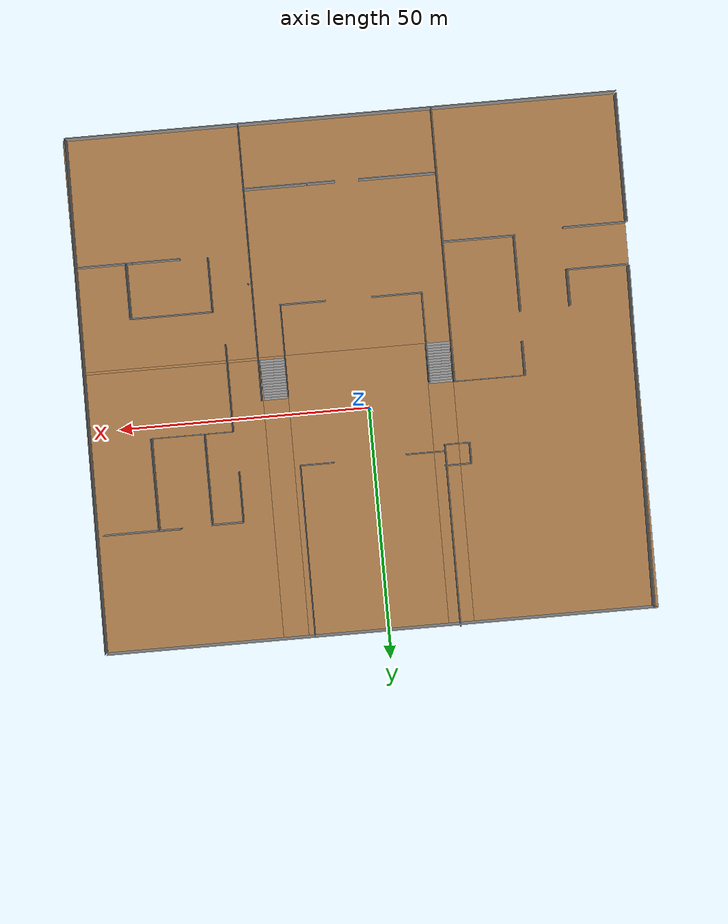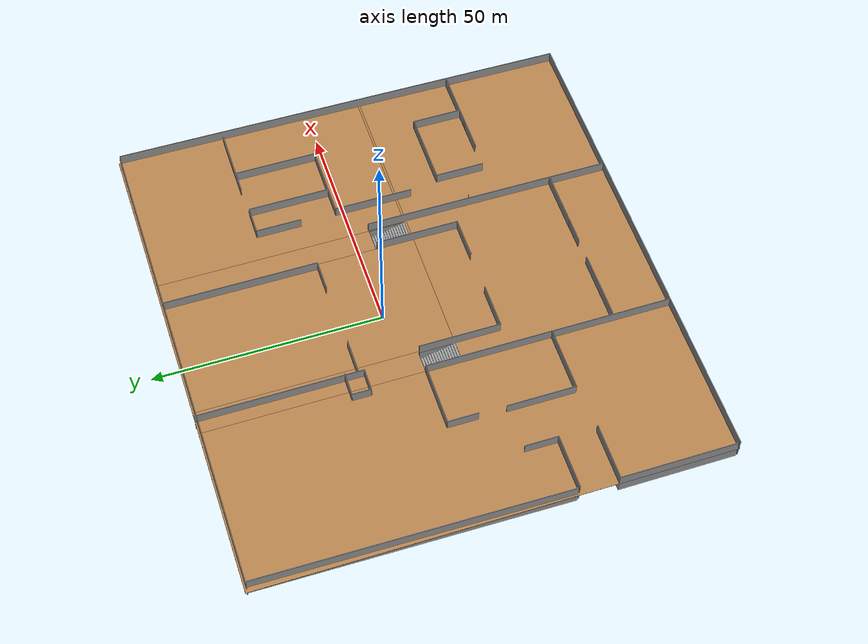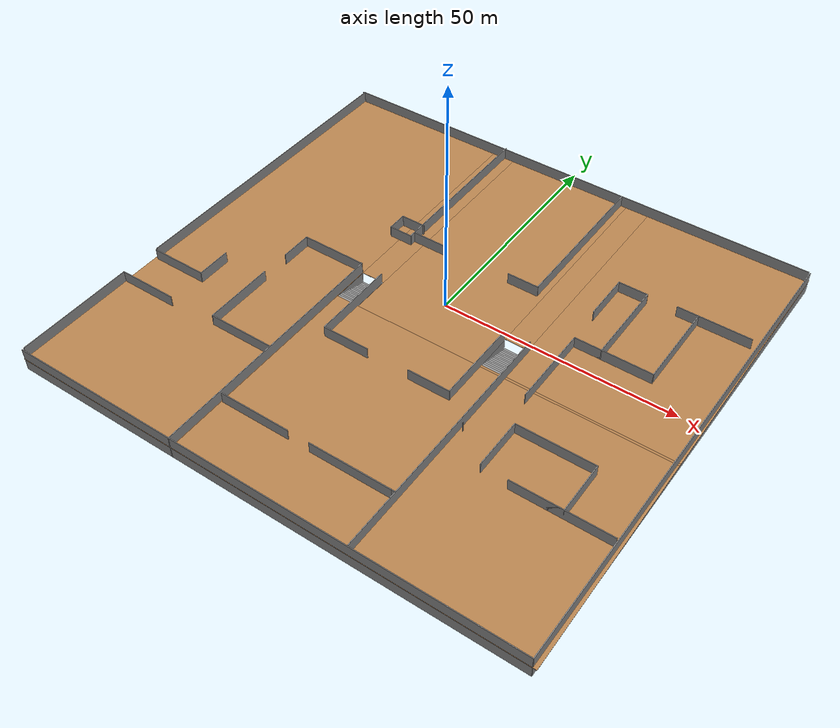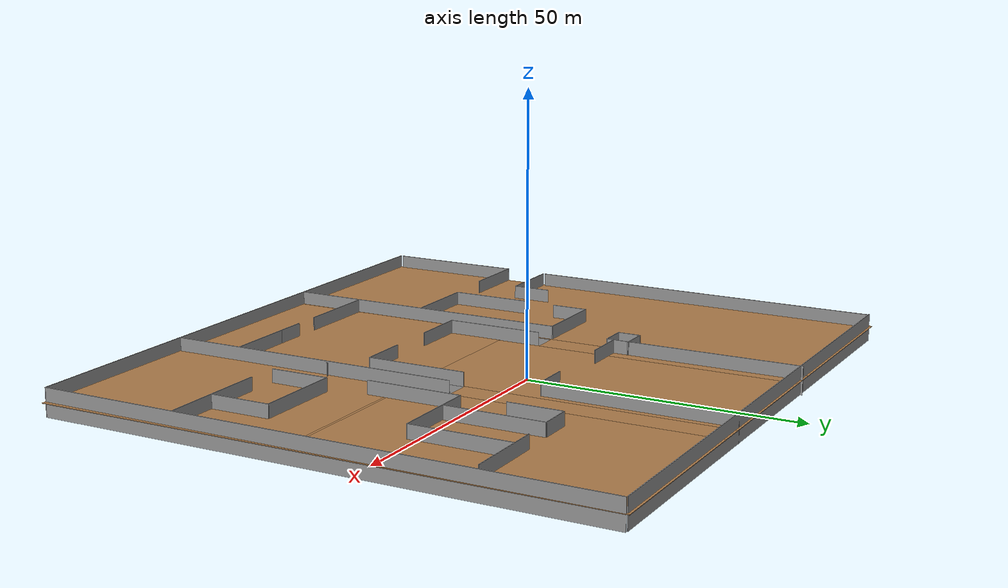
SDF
<?xml version='1.0'?>
<sdf version='1.6'>
  <model name='new_building'>
    <pose frame=''>1.10912 -6.88825 0 0 -0 0</pose>
    <link name='Floor_0'>
      <pose frame=''>0 1e-06 2.5 0 -0 0</pose>
      <visual name='Floor_0_Visual_0'>
        <pose frame=''>-36.3115 0 0.05 0 -0 0</pose>
        <geometry>
          <box>
            <size>36.4817 101.781 0.1</size>
          </box>
        </geometry>
        <material>
          <script>
            <uri>file://media/materials/scripts/gazebo.material</uri>
            <name>Gazebo/Wood</name>
          </script>
          <ambient>1 1 1 1</ambient>
        </material>
        <meta>
          <layer>1</layer>
        </meta>
      </visual>
      <collision name='Floor_0_Collision_0'>
        <geometry>
          <box>
            <size>36.4817 101.781 0.1</size>
          </box>
        </geometry>
        <pose frame=''>-36.3115 0 0.05 0 -0 0</pose>
      </collision>
      <visual name='Floor_0_Visual_1'>
        <pose frame=''>18.2409 -27.9329 0.05 0 -0 0</pose>
        <geometry>
          <box>
            <size>72.6231 45.9155 0.1</size>
          </box>
        </geometry>
        <material>
          <script>
            <uri>file://media/materials/scripts/gazebo.material</uri>
            <name>Gazebo/Wood</name>
          </script>
          <ambient>1 1 1 1</ambient>
        </material>
        <meta>
          <layer>1</layer>
        </meta>
      </visual>
      <collision name='Floor_0_Collision_1'>
        <geometry>
          <box>
            <size>72.6231 45.9155 0.1</size>
          </box>
        </geometry>
        <pose frame=''>18.2409 -27.9329 0.05 0 -0 0</pose>
      </collision>
      <visual name='Floor_0_Visual_2'>
        <pose frame=''>0.764911 22.9577 0.05 0 -0 0</pose>
        <geometry>
          <box>
            <size>27.6712 55.8658 0.1</size>
          </box>
        </geometry>
        <material>
          <script>
            <uri>file://media/materials/scripts/gazebo.material</uri>
            <name>Gazebo/Wood</name>
          </script>
          <ambient>1 1 1 1</ambient>
        </material>
        <meta>
          <layer>1</layer>
        </meta>
      </visual>
      <collision name='Floor_0_Collision_2'>
        <geometry>
          <box>
            <size>27.6712 55.8658 0.1</size>
          </box>
        </geometry>
        <pose frame=''>0.764911 22.9577 0.05 0 -0 0</pose>
      </collision>
      <visual name='Floor_0_Visual_3'>
        <pose frame=''>34.5765 -4.72762 0.05 0 -0 0</pose>
        <geometry>
          <box>
            <size>39.9519 0.495018 0.1</size>
          </box>
        </geometry>
        <material>
          <script>
            <uri>file://media/materials/scripts/gazebo.material</uri>
            <name>Gazebo/Wood</name>
          </script>
          <ambient>1 1 1 1</ambient>
        </material>
        <meta>
          <layer>1</layer>
        </meta>
      </visual>
      <collision name='Floor_0_Collision_3'>
        <geometry>
          <box>
            <size>39.9519 0.495018 0.1</size>
          </box>
        </geometry>
        <pose frame=''>34.5765 -4.72762 0.05 0 -0 0</pose>
      </collision>
      <visual name='Floor_0_Visual_4'>
        <pose frame=''>37.0765 23.2053 0.05 0 -0 0</pose>
        <geometry>
          <box>
            <size>34.9519 55.3707 0.1</size>
          </box>
        </geometry>
        <material>
          <script>
            <uri>file://media/materials/scripts/gazebo.material</uri>
            <name>Gazebo/Wood</name>
          </script>
          <ambient>1 1 1 1</ambient>
        </material>
        <meta>
          <layer>1</layer>
        </meta>
      </visual>
      <collision name='Floor_0_Collision_4'>
        <geometry>
          <box>
            <size>34.9519 55.3707 0.1</size>
          </box>
        </geometry>
        <pose frame=''>37.0765 23.2053 0.05 0 -0 0</pose>
      </collision>
      <visual name='Floor_0_Visual_5'>
        <pose frame=''>-15.5707 26.9577 0.05 0 -0 0</pose>
        <geometry>
          <box>
            <size>5 47.8658 0.1</size>
          </box>
        </geometry>
        <material>
          <script>
            <uri>file://media/materials/scripts/gazebo.material</uri>
            <name>Gazebo/Wood</name>
          </script>
          <ambient>1 1 1 1</ambient>
        </material>
        <meta>
          <layer>1</layer>
        </meta>
      </visual>
      <collision name='Floor_0_Collision_5'>
        <geometry>
          <box>
            <size>5 47.8658 0.1</size>
          </box>
        </geometry>
        <pose frame=''>-15.5707 26.9577 0.05 0 -0 0</pose>
      </collision>
      <visual name='Floor_0_Visual_6'>
        <pose frame=''>17.1005 27.2053 0.05 0 -0 0</pose>
        <geometry>
          <box>
            <size>5 47.3707 0.1</size>
          </box>
        </geometry>
        <material>
          <script>
            <uri>file://media/materials/scripts/gazebo.material</uri>
            <name>Gazebo/Wood</name>
          </script>
          <ambient>1 1 1 1</ambient>
        </material>
        <meta>
          <layer>1</layer>
        </meta>
      </visual>
      <collision name='Floor_0_Collision_6'>
        <geometry>
          <box>
            <size>5 47.3707 0.1</size>
          </box>
        </geometry>
        <pose frame=''>17.1005 27.2053 0.05 0 -0 0</pose>
      </collision>
    </link>
    <link name='Stairs_1'>
      <visual name='Stairs_1_Visual_0'>
        <pose frame=''>-15.5707 2.7582 0.083333 0 -0 0</pose>
        <geometry>
          <box>
            <size>5 0.533333 0.166667</size>
          </box>
        </geometry>
        <material>
          <script>
            <uri>file://media/materials/scripts/gazebo.material</uri>
            <name>Gazebo/Grey</name>
          </script>
          <ambient>1 1 1 1</ambient>
        </material>
        <meta>
          <layer>0</layer>
        </meta>
      </visual>
      <collision name='Stairs_1_Collision_0'>
        <geometry>
          <box>
            <size>5 0.533333 0.166667</size>
          </box>
        </geometry>
        <pose frame=''>-15.5707 2.7582 0.083333 0 -0 0</pose>
      </collision>
      <visual name='Stairs_1_Visual_1'>
        <pose frame=''>-15.5707 2.22487 0.25 0 -0 0</pose>
        <geometry>
          <box>
            <size>5 0.533333 0.166667</size>
          </box>
        </geometry>
        <material>
          <script>
            <uri>file://media/materials/scripts/gazebo.material</uri>
            <name>Gazebo/Grey</name>
          </script>
          <ambient>1 1 1 1</ambient>
        </material>
        <meta>
          <layer>0</layer>
        </meta>
      </visual>
      <collision name='Stairs_1_Collision_1'>
        <geometry>
          <box>
            <size>5 0.533333 0.166667</size>
          </box>
        </geometry>
        <pose frame=''>-15.5707 2.22487 0.25 0 -0 0</pose>
      </collision>
      <visual name='Stairs_1_Visual_2'>
        <pose frame=''>-15.5707 1.69154 0.416667 0 -0 0</pose>
        <geometry>
          <box>
            <size>5 0.533333 0.166667</size>
          </box>
        </geometry>
        <material>
          <script>
            <uri>file://media/materials/scripts/gazebo.material</uri>
            <name>Gazebo/Grey</name>
          </script>
          <ambient>1 1 1 1</ambient>
        </material>
        <meta>
          <layer>0</layer>
        </meta>
      </visual>
      <collision name='Stairs_1_Collision_2'>
        <geometry>
          <box>
            <size>5 0.533333 0.166667</size>
          </box>
        </geometry>
        <pose frame=''>-15.5707 1.69154 0.416667 0 -0 0</pose>
      </collision>
      <visual name='Stairs_1_Visual_3'>
        <pose frame=''>-15.5707 1.1582 0.583333 0 -0 0</pose>
        <geometry>
          <box>
            <size>5 0.533333 0.166667</size>
          </box>
        </geometry>
        <material>
          <script>
            <uri>file://media/materials/scripts/gazebo.material</uri>
            <name>Gazebo/Grey</name>
          </script>
          <ambient>1 1 1 1</ambient>
        </material>
        <meta>
          <layer>0</layer>
        </meta>
      </visual>
      <collision name='Stairs_1_Collision_3'>
        <geometry>
          <box>
            <size>5 0.533333 0.166667</size>
          </box>
        </geometry>
        <pose frame=''>-15.5707 1.1582 0.583333 0 -0 0</pose>
      </collision>
      <visual name='Stairs_1_Visual_4'>
        <pose frame=''>-15.5707 0.624868 0.75 0 -0 0</pose>
        <geometry>
          <box>
            <size>5 0.533333 0.166667</size>
          </box>
        </geometry>
        <material>
          <script>
            <uri>file://media/materials/scripts/gazebo.material</uri>
            <name>Gazebo/Grey</name>
          </script>
          <ambient>1 1 1 1</ambient>
        </material>
        <meta>
          <layer>0</layer>
        </meta>
      </visual>
      <collision name='Stairs_1_Collision_4'>
        <geometry>
          <box>
            <size>5 0.533333 0.166667</size>
          </box>
        </geometry>
        <pose frame=''>-15.5707 0.624868 0.75 0 -0 0</pose>
      </collision>
      <visual name='Stairs_1_Visual_5'>
        <pose frame=''>-15.5707 0.091535 0.916667 0 -0 0</pose>
        <geometry>
          <box>
            <size>5 0.533333 0.166667</size>
          </box>
        </geometry>
        <material>
          <script>
            <uri>file://media/materials/scripts/gazebo.material</uri>
            <name>Gazebo/Grey</name>
          </script>
          <ambient>1 1 1 1</ambient>
        </material>
        <meta>
          <layer>0</layer>
        </meta>
      </visual>
      <collision name='Stairs_1_Collision_5'>
        <geometry>
          <box>
            <size>5 0.533333 0.166667</size>
          </box>
        </geometry>
        <pose frame=''>-15.5707 0.091535 0.916667 0 -0 0</pose>
      </collision>
      <visual name='Stairs_1_Visual_6'>
        <pose frame=''>-15.5707 -0.441798 1.08333 0 -0 0</pose>
        <geometry>
          <box>
            <size>5 0.533333 0.166667</size>
          </box>
        </geometry>
        <material>
          <script>
            <uri>file://media/materials/scripts/gazebo.material</uri>
            <name>Gazebo/Grey</name>
          </script>
          <ambient>1 1 1 1</ambient>
        </material>
        <meta>
          <layer>0</layer>
        </meta>
      </visual>
      <collision name='Stairs_1_Collision_6'>
        <geometry>
          <box>
            <size>5 0.533333 0.166667</size>
          </box>
        </geometry>
        <pose frame=''>-15.5707 -0.441798 1.08333 0 -0 0</pose>
      </collision>
      <visual name='Stairs_1_Visual_7'>
        <pose frame=''>-15.5707 -0.975132 1.25 0 -0 0</pose>
        <geometry>
          <box>
            <size>5 0.533333 0.166667</size>
          </box>
        </geometry>
        <material>
          <script>
            <uri>file://media/materials/scripts/gazebo.material</uri>
            <name>Gazebo/Grey</name>
          </script>
          <ambient>1 1 1 1</ambient>
        </material>
        <meta>
          <layer>0</layer>
        </meta>
      </visual>
      <collision name='Stairs_1_Collision_7'>
        <geometry>
          <box>
            <size>5 0.533333 0.166667</size>
          </box>
        </geometry>
        <pose frame=''>-15.5707 -0.975132 1.25 0 -0 0</pose>
      </collision>
      <visual name='Stairs_1_Visual_8'>
        <pose frame=''>-15.5707 -1.50846 1.41667 0 -0 0</pose>
        <geometry>
          <box>
            <size>5 0.533333 0.166667</size>
          </box>
        </geometry>
        <material>
          <script>
            <uri>file://media/materials/scripts/gazebo.material</uri>
            <name>Gazebo/Grey</name>
          </script>
          <ambient>1 1 1 1</ambient>
        </material>
        <meta>
          <layer>0</layer>
        </meta>
      </visual>
      <collision name='Stairs_1_Collision_8'>
        <geometry>
          <box>
            <size>5 0.533333 0.166667</size>
          </box>
        </geometry>
        <pose frame=''>-15.5707 -1.50846 1.41667 0 -0 0</pose>
      </collision>
      <visual name='Stairs_1_Visual_9'>
        <pose frame=''>-15.5707 -2.0418 1.58333 0 -0 0</pose>
        <geometry>
          <box>
            <size>5 0.533333 0.166667</size>
          </box>
        </geometry>
        <material>
          <script>
            <uri>file://media/materials/scripts/gazebo.material</uri>
            <name>Gazebo/Grey</name>
          </script>
          <ambient>1 1 1 1</ambient>
        </material>
        <meta>
          <layer>0</layer>
        </meta>
      </visual>
      <collision name='Stairs_1_Collision_9'>
        <geometry>
          <box>
            <size>5 0.533333 0.166667</size>
          </box>
        </geometry>
        <pose frame=''>-15.5707 -2.0418 1.58333 0 -0 0</pose>
      </collision>
      <visual name='Stairs_1_Visual_10'>
        <pose frame=''>-15.5707 -2.57513 1.75 0 -0 0</pose>
        <geometry>
          <box>
            <size>5 0.533333 0.166667</size>
          </box>
        </geometry>
        <material>
          <script>
            <uri>file://media/materials/scripts/gazebo.material</uri>
            <name>Gazebo/Grey</name>
          </script>
          <ambient>1 1 1 1</ambient>
        </material>
        <meta>
          <layer>0</layer>
        </meta>
      </visual>
      <collision name='Stairs_1_Collision_10'>
        <geometry>
          <box>
            <size>5 0.533333 0.166667</size>
          </box>
        </geometry>
        <pose frame=''>-15.5707 -2.57513 1.75 0 -0 0</pose>
      </collision>
      <visual name='Stairs_1_Visual_11'>
        <pose frame=''>-15.5707 -3.10846 1.91667 0 -0 0</pose>
        <geometry>
          <box>
            <size>5 0.533333 0.166667</size>
          </box>
        </geometry>
        <material>
          <script>
            <uri>file://media/materials/scripts/gazebo.material</uri>
            <name>Gazebo/Grey</name>
          </script>
          <ambient>1 1 1 1</ambient>
        </material>
        <meta>
          <layer>0</layer>
        </meta>
      </visual>
      <collision name='Stairs_1_Collision_11'>
        <geometry>
          <box>
            <size>5 0.533333 0.166667</size>
          </box>
        </geometry>
        <pose frame=''>-15.5707 -3.10846 1.91667 0 -0 0</pose>
      </collision>
      <visual name='Stairs_1_Visual_12'>
        <pose frame=''>-15.5707 -3.6418 2.08333 0 -0 0</pose>
        <geometry>
          <box>
            <size>5 0.533333 0.166667</size>
          </box>
        </geometry>
        <material>
          <script>
            <uri>file://media/materials/scripts/gazebo.material</uri>
            <name>Gazebo/Grey</name>
          </script>
          <ambient>1 1 1 1</ambient>
        </material>
        <meta>
          <layer>0</layer>
        </meta>
      </visual>
      <collision name='Stairs_1_Collision_12'>
        <geometry>
          <box>
            <size>5 0.533333 0.166667</size>
          </box>
        </geometry>
        <pose frame=''>-15.5707 -3.6418 2.08333 0 -0 0</pose>
      </collision>
      <visual name='Stairs_1_Visual_13'>
        <pose frame=''>-15.5707 -4.17513 2.25 0 -0 0</pose>
        <geometry>
          <box>
            <size>5 0.533333 0.166667</size>
          </box>
        </geometry>
        <material>
          <script>
            <uri>file://media/materials/scripts/gazebo.material</uri>
            <name>Gazebo/Grey</name>
          </script>
          <ambient>1 1 1 1</ambient>
        </material>
        <meta>
          <layer>0</layer>
        </meta>
      </visual>
      <collision name='Stairs_1_Collision_13'>
        <geometry>
          <box>
            <size>5 0.533333 0.166667</size>
          </box>
        </geometry>
        <pose frame=''>-15.5707 -4.17513 2.25 0 -0 0</pose>
      </collision>
      <visual name='Stairs_1_Visual_14'>
        <pose frame=''>-15.5707 -4.70847 2.41667 0 -0 0</pose>
        <geometry>
          <box>
            <size>5 0.533333 0.166667</size>
          </box>
        </geometry>
        <material>
          <script>
            <uri>file://media/materials/scripts/gazebo.material</uri>
            <name>Gazebo/Grey</name>
          </script>
          <ambient>1 1 1 1</ambient>
        </material>
        <meta>
          <layer>0</layer>
        </meta>
      </visual>
      <collision name='Stairs_1_Collision_14'>
        <geometry>
          <box>
            <size>5 0.533333 0.166667</size>
          </box>
        </geometry>
        <pose frame=''>-15.5707 -4.70847 2.41667 0 -0 0</pose>
      </collision>
    </link>
    <link name='Stairs_2'>
      <visual name='Stairs_2_Visual_0'>
        <pose frame=''>17.1005 3.25322 0.083333 0 -0 0</pose>
        <geometry>
          <box>
            <size>5 0.533333 0.166667</size>
          </box>
        </geometry>
        <material>
          <script>
            <uri>file://media/materials/scripts/gazebo.material</uri>
            <name>Gazebo/Grey</name>
          </script>
          <ambient>1 1 1 1</ambient>
        </material>
        <meta>
          <layer>0</layer>
        </meta>
      </visual>
      <collision name='Stairs_2_Collision_0'>
        <geometry>
          <box>
            <size>5 0.533333 0.166667</size>
          </box>
        </geometry>
        <pose frame=''>17.1005 3.25322 0.083333 0 -0 0</pose>
      </collision>
      <visual name='Stairs_2_Visual_1'>
        <pose frame=''>17.1005 2.71989 0.25 0 -0 0</pose>
        <geometry>
          <box>
            <size>5 0.533333 0.166667</size>
          </box>
        </geometry>
        <material>
          <script>
            <uri>file://media/materials/scripts/gazebo.material</uri>
            <name>Gazebo/Grey</name>
          </script>
          <ambient>1 1 1 1</ambient>
        </material>
        <meta>
          <layer>0</layer>
        </meta>
      </visual>
      <collision name='Stairs_2_Collision_1'>
        <geometry>
          <box>
            <size>5 0.533333 0.166667</size>
          </box>
        </geometry>
        <pose frame=''>17.1005 2.71989 0.25 0 -0 0</pose>
      </collision>
      <visual name='Stairs_2_Visual_2'>
        <pose frame=''>17.1005 2.18655 0.416667 0 -0 0</pose>
        <geometry>
          <box>
            <size>5 0.533333 0.166667</size>
          </box>
        </geometry>
        <material>
          <script>
            <uri>file://media/materials/scripts/gazebo.material</uri>
            <name>Gazebo/Grey</name>
          </script>
          <ambient>1 1 1 1</ambient>
        </material>
        <meta>
          <layer>0</layer>
        </meta>
      </visual>
      <collision name='Stairs_2_Collision_2'>
        <geometry>
          <box>
            <size>5 0.533333 0.166667</size>
          </box>
        </geometry>
        <pose frame=''>17.1005 2.18655 0.416667 0 -0 0</pose>
      </collision>
      <visual name='Stairs_2_Visual_3'>
        <pose frame=''>17.1005 1.65322 0.583333 0 -0 0</pose>
        <geometry>
          <box>
            <size>5 0.533333 0.166667</size>
          </box>
        </geometry>
        <material>
          <script>
            <uri>file://media/materials/scripts/gazebo.material</uri>
            <name>Gazebo/Grey</name>
          </script>
          <ambient>1 1 1 1</ambient>
        </material>
        <meta>
          <layer>0</layer>
        </meta>
      </visual>
      <collision name='Stairs_2_Collision_3'>
        <geometry>
          <box>
            <size>5 0.533333 0.166667</size>
          </box>
        </geometry>
        <pose frame=''>17.1005 1.65322 0.583333 0 -0 0</pose>
      </collision>
      <visual name='Stairs_2_Visual_4'>
        <pose frame=''>17.1005 1.11989 0.75 0 -0 0</pose>
        <geometry>
          <box>
            <size>5 0.533333 0.166667</size>
          </box>
        </geometry>
        <material>
          <script>
            <uri>file://media/materials/scripts/gazebo.material</uri>
            <name>Gazebo/Grey</name>
          </script>
          <ambient>1 1 1 1</ambient>
        </material>
        <meta>
          <layer>0</layer>
        </meta>
      </visual>
      <collision name='Stairs_2_Collision_4'>
        <geometry>
          <box>
            <size>5 0.533333 0.166667</size>
          </box>
        </geometry>
        <pose frame=''>17.1005 1.11989 0.75 0 -0 0</pose>
      </collision>
      <visual name='Stairs_2_Visual_5'>
        <pose frame=''>17.1005 0.586554 0.916667 0 -0 0</pose>
        <geometry>
          <box>
            <size>5 0.533333 0.166667</size>
          </box>
        </geometry>
        <material>
          <script>
            <uri>file://media/materials/scripts/gazebo.material</uri>
            <name>Gazebo/Grey</name>
          </script>
          <ambient>1 1 1 1</ambient>
        </material>
        <meta>
          <layer>0</layer>
        </meta>
      </visual>
      <collision name='Stairs_2_Collision_5'>
        <geometry>
          <box>
            <size>5 0.533333 0.166667</size>
          </box>
        </geometry>
        <pose frame=''>17.1005 0.586554 0.916667 0 -0 0</pose>
      </collision>
      <visual name='Stairs_2_Visual_6'>
        <pose frame=''>17.1005 0.05322 1.08333 0 -0 0</pose>
        <geometry>
          <box>
            <size>5 0.533333 0.166667</size>
          </box>
        </geometry>
        <material>
          <script>
            <uri>file://media/materials/scripts/gazebo.material</uri>
            <name>Gazebo/Grey</name>
          </script>
          <ambient>1 1 1 1</ambient>
        </material>
        <meta>
          <layer>0</layer>
        </meta>
      </visual>
      <collision name='Stairs_2_Collision_6'>
        <geometry>
          <box>
            <size>5 0.533333 0.166667</size>
          </box>
        </geometry>
        <pose frame=''>17.1005 0.05322 1.08333 0 -0 0</pose>
      </collision>
      <visual name='Stairs_2_Visual_7'>
        <pose frame=''>17.1005 -0.480113 1.25 0 -0 0</pose>
        <geometry>
          <box>
            <size>5 0.533333 0.166667</size>
          </box>
        </geometry>
        <material>
          <script>
            <uri>file://media/materials/scripts/gazebo.material</uri>
            <name>Gazebo/Grey</name>
          </script>
          <ambient>1 1 1 1</ambient>
        </material>
        <meta>
          <layer>0</layer>
        </meta>
      </visual>
      <collision name='Stairs_2_Collision_7'>
        <geometry>
          <box>
            <size>5 0.533333 0.166667</size>
          </box>
        </geometry>
        <pose frame=''>17.1005 -0.480113 1.25 0 -0 0</pose>
      </collision>
      <visual name='Stairs_2_Visual_8'>
        <pose frame=''>17.1005 -1.01345 1.41667 0 -0 0</pose>
        <geometry>
          <box>
            <size>5 0.533333 0.166667</size>
          </box>
        </geometry>
        <material>
          <script>
            <uri>file://media/materials/scripts/gazebo.material</uri>
            <name>Gazebo/Grey</name>
          </script>
          <ambient>1 1 1 1</ambient>
        </material>
        <meta>
          <layer>0</layer>
        </meta>
      </visual>
      <collision name='Stairs_2_Collision_8'>
        <geometry>
          <box>
            <size>5 0.533333 0.166667</size>
          </box>
        </geometry>
        <pose frame=''>17.1005 -1.01345 1.41667 0 -0 0</pose>
      </collision>
      <visual name='Stairs_2_Visual_9'>
        <pose frame=''>17.1005 -1.54678 1.58333 0 -0 0</pose>
        <geometry>
          <box>
            <size>5 0.533333 0.166667</size>
          </box>
        </geometry>
        <material>
          <script>
            <uri>file://media/materials/scripts/gazebo.material</uri>
            <name>Gazebo/Grey</name>
          </script>
          <ambient>1 1 1 1</ambient>
        </material>
        <meta>
          <layer>0</layer>
        </meta>
      </visual>
      <collision name='Stairs_2_Collision_9'>
        <geometry>
          <box>
            <size>5 0.533333 0.166667</size>
          </box>
        </geometry>
        <pose frame=''>17.1005 -1.54678 1.58333 0 -0 0</pose>
      </collision>
      <visual name='Stairs_2_Visual_10'>
        <pose frame=''>17.1005 -2.08011 1.75 0 -0 0</pose>
        <geometry>
          <box>
            <size>5 0.533333 0.166667</size>
          </box>
        </geometry>
        <material>
          <script>
            <uri>file://media/materials/scripts/gazebo.material</uri>
            <name>Gazebo/Grey</name>
          </script>
          <ambient>1 1 1 1</ambient>
        </material>
        <meta>
          <layer>0</layer>
        </meta>
      </visual>
      <collision name='Stairs_2_Collision_10'>
        <geometry>
          <box>
            <size>5 0.533333 0.166667</size>
          </box>
        </geometry>
        <pose frame=''>17.1005 -2.08011 1.75 0 -0 0</pose>
      </collision>
      <visual name='Stairs_2_Visual_11'>
        <pose frame=''>17.1005 -2.61345 1.91667 0 -0 0</pose>
        <geometry>
          <box>
            <size>5 0.533333 0.166667</size>
          </box>
        </geometry>
        <material>
          <script>
            <uri>file://media/materials/scripts/gazebo.material</uri>
            <name>Gazebo/Grey</name>
          </script>
          <ambient>1 1 1 1</ambient>
        </material>
        <meta>
          <layer>0</layer>
        </meta>
      </visual>
      <collision name='Stairs_2_Collision_11'>
        <geometry>
          <box>
            <size>5 0.533333 0.166667</size>
          </box>
        </geometry>
        <pose frame=''>17.1005 -2.61345 1.91667 0 -0 0</pose>
      </collision>
      <visual name='Stairs_2_Visual_12'>
        <pose frame=''>17.1005 -3.14678 2.08333 0 -0 0</pose>
        <geometry>
          <box>
            <size>5 0.533333 0.166667</size>
          </box>
        </geometry>
        <material>
          <script>
            <uri>file://media/materials/scripts/gazebo.material</uri>
            <name>Gazebo/Grey</name>
          </script>
          <ambient>1 1 1 1</ambient>
        </material>
        <meta>
          <layer>0</layer>
        </meta>
      </visual>
      <collision name='Stairs_2_Collision_12'>
        <geometry>
          <box>
            <size>5 0.533333 0.166667</size>
          </box>
        </geometry>
        <pose frame=''>17.1005 -3.14678 2.08333 0 -0 0</pose>
      </collision>
      <visual name='Stairs_2_Visual_13'>
        <pose frame=''>17.1005 -3.68011 2.25 0 -0 0</pose>
        <geometry>
          <box>
            <size>5 0.533333 0.166667</size>
          </box>
        </geometry>
        <material>
          <script>
            <uri>file://media/materials/scripts/gazebo.material</uri>
            <name>Gazebo/Grey</name>
          </script>
          <ambient>1 1 1 1</ambient>
        </material>
        <meta>
          <layer>0</layer>
        </meta>
      </visual>
      <collision name='Stairs_2_Collision_13'>
        <geometry>
          <box>
            <size>5 0.533333 0.166667</size>
          </box>
        </geometry>
        <pose frame=''>17.1005 -3.68011 2.25 0 -0 0</pose>
      </collision>
      <visual name='Stairs_2_Visual_14'>
        <pose frame=''>17.1005 -4.21345 2.41667 0 -0 0</pose>
        <geometry>
          <box>
            <size>5 0.533333 0.166667</size>
          </box>
        </geometry>
        <material>
          <script>
            <uri>file://media/materials/scripts/gazebo.material</uri>
            <name>Gazebo/Grey</name>
          </script>
          <ambient>1 1 1 1</ambient>
        </material>
        <meta>
          <layer>0</layer>
        </meta>
      </visual>
      <collision name='Stairs_2_Collision_14'>
        <geometry>
          <box>
            <size>5 0.533333 0.166667</size>
          </box>
        </geometry>
        <pose frame=''>17.1005 -4.21345 2.41667 0 -0 0</pose>
      </collision>
    </link>
    <link name='Wall_10'>
      <collision name='Wall_10_Collision'>
        <geometry>
          <box>
            <size>25.25 0.15 2.5</size>
          </box>
        </geometry>
        <pose frame=''>0 0 1.25 0 -0 0</pose>
      </collision>
      <visual name='Wall_10_Visual'>
        <pose frame=''>0 0 1.25 0 -0 0</pose>
        <geometry>
          <box>
            <size>25.25 0.15 2.5</size>
          </box>
        </geometry>
        <material>
          <script>
            <uri>file://media/materials/scripts/gazebo.material</uri>
            <name>Gazebo/Grey</name>
          </script>
          <ambient>1 1 1 1</ambient>
        </material>
        <meta>
          <layer>0</layer>
        </meta>
      </visual>
      <pose frame=''>-54.4774 -37.7529 0 0 -0 1.5708</pose>
    </link>
    <link name='Wall_100'>
      <collision name='Wall_100_Collision'>
        <geometry>
          <box>
            <size>5 0.15 2.5</size>
          </box>
        </geometry>
        <pose frame=''>0 0 1.25 0 -0 0</pose>
      </collision>
      <visual name='Wall_100_Visual'>
        <pose frame=''>0 0 1.25 0 -0 0</pose>
        <geometry>
          <box>
            <size>5 0.15 2.5</size>
          </box>
        </geometry>
        <material>
          <script>
            <uri>file://media/materials/scripts/gazebo.material</uri>
            <name>Gazebo/Grey</name>
          </script>
          <ambient>1 1 1 1</ambient>
        </material>
        <meta>
          <layer>1</layer>
        </meta>
      </visual>
      <pose frame=''>-17.6842 15.2156 2.5 0 -0 3.14159</pose>
    </link>
    <link name='Wall_101'>
      <collision name='Wall_101_Collision'>
        <geometry>
          <box>
            <size>4.25 0.15 2.5</size>
          </box>
        </geometry>
        <pose frame=''>0 0 1.25 0 -0 0</pose>
      </collision>
      <visual name='Wall_101_Visual'>
        <pose frame=''>0 0 1.25 0 -0 0</pose>
        <geometry>
          <box>
            <size>4.25 0.15 2.5</size>
          </box>
        </geometry>
        <material>
          <script>
            <uri>file://media/materials/scripts/gazebo.material</uri>
            <name>Gazebo/Grey</name>
          </script>
          <ambient>1 1 1 1</ambient>
        </material>
        <meta>
          <layer>1</layer>
        </meta>
      </visual>
      <pose frame=''>-20.1092 17.2656 2.5 0 -0 1.5708</pose>
    </link>
    <link name='Wall_102'>
      <collision name='Wall_102_Collision'>
        <geometry>
          <box>
            <size>5.25 0.15 2.5</size>
          </box>
        </geometry>
        <pose frame=''>0 0 1.25 0 -0 0</pose>
      </collision>
      <visual name='Wall_102_Visual'>
        <pose frame=''>0 0 1.25 0 -0 0</pose>
        <geometry>
          <box>
            <size>5.25 0.15 2.5</size>
          </box>
        </geometry>
        <material>
          <script>
            <uri>file://media/materials/scripts/gazebo.material</uri>
            <name>Gazebo/Grey</name>
          </script>
          <ambient>1 1 1 1</ambient>
        </material>
        <meta>
          <layer>1</layer>
        </meta>
      </visual>
      <pose frame=''>-17.5592 19.3156 2.5 0 -0 0</pose>
    </link>
    <link name='Wall_103'>
      <collision name='Wall_103_Collision'>
        <geometry>
          <box>
            <size>33.75 0.15 2.5</size>
          </box>
        </geometry>
        <pose frame=''>0 0 1.25 0 -0 0</pose>
      </collision>
      <visual name='Wall_103_Visual'>
        <pose frame=''>0 0 1.25 0 -0 0</pose>
        <geometry>
          <box>
            <size>33.75 0.15 2.5</size>
          </box>
        </geometry>
        <material>
          <script>
            <uri>file://media/materials/scripts/gazebo.material</uri>
            <name>Gazebo/Grey</name>
          </script>
          <ambient>1 1 1 1</ambient>
        </material>
        <meta>
          <layer>1</layer>
        </meta>
      </visual>
      <pose frame=''>13.35 33.6562 2.5 0 -0 -1.5708</pose>
    </link>
    <link name='Wall_104'>
      <collision name='Wall_104_Collision'>
        <geometry>
          <box>
            <size>6.75 0.15 2.5</size>
          </box>
        </geometry>
        <pose frame=''>0 0 1.25 0 -0 0</pose>
      </collision>
      <visual name='Wall_104_Visual'>
        <pose frame=''>0 0 1.25 0 -0 0</pose>
        <geometry>
          <box>
            <size>6.75 0.15 2.5</size>
          </box>
        </geometry>
        <material>
          <script>
            <uri>file://media/materials/scripts/gazebo.material</uri>
            <name>Gazebo/Grey</name>
          </script>
          <ambient>1 1 1 1</ambient>
        </material>
        <meta>
          <layer>1</layer>
        </meta>
      </visual>
      <pose frame=''>10.05 16.8562 2.5 0 -0 3.14159</pose>
    </link>
    <link name='Wall_105'>
      <collision name='Wall_105_Collision'>
        <geometry>
          <box>
            <size>7.75 0.15 2.5</size>
          </box>
        </geometry>
        <pose frame=''>0 0 1.25 0 -0 0</pose>
      </collision>
      <visual name='Wall_105_Visual'>
        <pose frame=''>0 0 1.25 0 -0 0</pose>
        <geometry>
          <box>
            <size>7.75 0.15 2.5</size>
          </box>
        </geometry>
        <material>
          <script>
            <uri>file://media/materials/scripts/gazebo.material</uri>
            <name>Gazebo/Grey</name>
          </script>
          <ambient>1 1 1 1</ambient>
        </material>
        <meta>
          <layer>1</layer>
        </meta>
      </visual>
      <pose frame=''>-11.3933 16.4836 2.5 0 -0 0</pose>
    </link>
    <link name='Wall_106'>
      <collision name='Wall_106_Collision'>
        <geometry>
          <box>
            <size>15.25 0.15 2.5</size>
          </box>
        </geometry>
        <pose frame=''>0 0 1.25 0 -0 0</pose>
      </collision>
      <visual name='Wall_106_Visual'>
        <pose frame=''>0 0 1.25 0 -0 0</pose>
        <geometry>
          <box>
            <size>15.25 0.15 2.5</size>
          </box>
        </geometry>
        <material>
          <script>
            <uri>file://media/materials/scripts/gazebo.material</uri>
            <name>Gazebo/Grey</name>
          </script>
          <ambient>1 1 1 1</ambient>
        </material>
        <meta>
          <layer>1</layer>
        </meta>
      </visual>
      <pose frame=''>45.2246 27.2094 2.5 0 -0 3.14159</pose>
    </link>
    <link name='Wall_107'>
      <collision name='Wall_107_Collision'>
        <geometry>
          <box>
            <size>4.5 0.15 2.5</size>
          </box>
        </geometry>
        <pose frame=''>0 0 1.25 0 -0 0</pose>
      </collision>
      <visual name='Wall_107_Visual'>
        <pose frame=''>0 0 1.25 0 -0 0</pose>
        <geometry>
          <box>
            <size>4.5 0.15 2.5</size>
          </box>
        </geometry>
        <material>
          <script>
            <uri>file://media/materials/scripts/gazebo.material</uri>
            <name>Gazebo/Grey</name>
          </script>
          <ambient>1 1 1 1</ambient>
        </material>
        <meta>
          <layer>1</layer>
        </meta>
      </visual>
      <pose frame=''>39.8496 27.2094 2.5 0 -0 0</pose>
    </link>
    <link name='Wall_108'>
      <collision name='Wall_108_Collision'>
        <geometry>
          <box>
            <size>18.25 0.15 2.5</size>
          </box>
        </geometry>
        <pose frame=''>0 0 1.25 0 -0 0</pose>
      </collision>
      <visual name='Wall_108_Visual'>
        <pose frame=''>0 0 1.25 0 -0 0</pose>
        <geometry>
          <box>
            <size>18.25 0.15 2.5</size>
          </box>
        </geometry>
        <material>
          <script>
            <uri>file://media/materials/scripts/gazebo.material</uri>
            <name>Gazebo/Grey</name>
          </script>
          <ambient>1 1 1 1</ambient>
        </material>
        <meta>
          <layer>1</layer>
        </meta>
      </visual>
      <pose frame=''>42.0246 18.1594 2.5 0 -0 -1.5708</pose>
    </link>
    <link name='Wall_109'>
      <collision name='Wall_109_Collision'>
        <geometry>
          <box>
            <size>16.25 0.15 2.5</size>
          </box>
        </geometry>
        <pose frame=''>0 0 1.25 0 -0 0</pose>
      </collision>
      <visual name='Wall_109_Visual'>
        <pose frame=''>0 0 1.25 0 -0 0</pose>
        <geometry>
          <box>
            <size>16.25 0.15 2.5</size>
          </box>
        </geometry>
        <material>
          <script>
            <uri>file://media/materials/scripts/gazebo.material</uri>
            <name>Gazebo/Grey</name>
          </script>
          <ambient>1 1 1 1</ambient>
        </material>
        <meta>
          <layer>1</layer>
        </meta>
      </visual>
      <pose frame=''>33.9746 9.10941 2.5 0 -0 3.14159</pose>
    </link>
    <link name='Wall_11'>
      <collision name='Wall_11_Collision'>
        <geometry>
          <box>
            <size>12.5 0.15 2.5</size>
          </box>
        </geometry>
        <pose frame=''>0 0 1.25 0 -0 0</pose>
      </collision>
      <visual name='Wall_11_Visual'>
        <pose frame=''>0 0 1.25 0 -0 0</pose>
        <geometry>
          <box>
            <size>12.5 0.15 2.5</size>
          </box>
        </geometry>
        <material>
          <script>
            <uri>file://media/materials/scripts/gazebo.material</uri>
            <name>Gazebo/CeilingTiled</name>
          </script>
          <ambient>1 1 1 1</ambient>
        </material>
        <meta>
          <layer>0</layer>
        </meta>
      </visual>
      <pose frame=''>-48.3024 -25.2029 0 0 -0 0</pose>
    </link>
    <link name='Wall_110'>
      <collision name='Wall_110_Collision'>
        <geometry>
          <box>
            <size>5.75 0.15 2.5</size>
          </box>
        </geometry>
        <pose frame=''>0 0 1.25 0 -0 0</pose>
      </collision>
      <visual name='Wall_110_Visual'>
        <pose frame=''>0 0 1.25 0 -0 0</pose>
        <geometry>
          <box>
            <size>5.75 0.15 2.5</size>
          </box>
        </geometry>
        <material>
          <script>
            <uri>file://media/materials/scripts/gazebo.material</uri>
            <name>Gazebo/Grey</name>
          </script>
          <ambient>1 1 1 1</ambient>
        </material>
        <meta>
          <layer>1</layer>
        </meta>
      </visual>
      <pose frame=''>28.7246 9.10941 2.5 0 -0 0</pose>
    </link>
    <link name='Wall_111'>
      <collision name='Wall_111_Collision'>
        <geometry>
          <box>
            <size>18 0.15 2.5</size>
          </box>
        </geometry>
        <pose frame=''>0 0 1.25 0 -0 0</pose>
      </collision>
      <visual name='Wall_111_Visual'>
        <pose frame=''>0 0 1.25 0 -0 0</pose>
        <geometry>
          <box>
            <size>18 0.15 2.5</size>
          </box>
        </geometry>
        <material>
          <script>
            <uri>file://media/materials/scripts/gazebo.material</uri>
            <name>Gazebo/Grey</name>
          </script>
          <ambient>1 1 1 1</ambient>
        </material>
        <meta>
          <layer>1</layer>
        </meta>
      </visual>
      <pose frame=''>31.5246 18.0344 2.5 0 -0 1.5708</pose>
    </link>
    <link name='Wall_112'>
      <collision name='Wall_112_Collision'>
        <geometry>
          <box>
            <size>6.25 0.15 2.5</size>
          </box>
        </geometry>
        <pose frame=''>0 0 1.25 0 -0 0</pose>
      </collision>
      <visual name='Wall_112_Visual'>
        <pose frame=''>0 0 1.25 0 -0 0</pose>
        <geometry>
          <box>
            <size>6.25 0.15 2.5</size>
          </box>
        </geometry>
        <material>
          <script>
            <uri>file://media/materials/scripts/gazebo.material</uri>
            <name>Gazebo/Grey</name>
          </script>
          <ambient>1 1 1 1</ambient>
        </material>
        <meta>
          <layer>1</layer>
        </meta>
      </visual>
      <pose frame=''>28.4746 26.9594 2.5 0 -0 3.14159</pose>
    </link>
    <link name='Wall_113'>
      <collision name='Wall_113_Collision'>
        <geometry>
          <box>
            <size>10 0.15 2.5</size>
          </box>
        </geometry>
        <pose frame=''>0 0 1.25 0 -0 0</pose>
      </collision>
      <visual name='Wall_113_Visual'>
        <pose frame=''>0 0 1.25 0 -0 0</pose>
        <geometry>
          <box>
            <size>10 0.15 2.5</size>
          </box>
        </geometry>
        <material>
          <script>
            <uri>file://media/materials/scripts/gazebo.material</uri>
            <name>Gazebo/Grey</name>
          </script>
          <ambient>1 1 1 1</ambient>
        </material>
        <meta>
          <layer>1</layer>
        </meta>
      </visual>
      <pose frame=''>25.4246 22.0344 2.5 0 -0 -1.5708</pose>
    </link>
    <link name='Wall_114'>
      <collision name='Wall_114_Collision'>
        <geometry>
          <box>
            <size>17.25 0.15 2.5</size>
          </box>
        </geometry>
        <pose frame=''>0 0 1.25 0 -0 0</pose>
      </collision>
      <visual name='Wall_114_Visual'>
        <pose frame=''>0 0 1.25 0 -0 0</pose>
        <geometry>
          <box>
            <size>17.25 0.15 2.5</size>
          </box>
        </geometry>
        <material>
          <script>
            <uri>file://media/materials/scripts/gazebo.material</uri>
            <name>Gazebo/Grey</name>
          </script>
          <ambient>1 1 1 1</ambient>
        </material>
        <meta>
          <layer>1</layer>
        </meta>
      </visual>
      <pose frame=''>25.9246 0.55941 2.5 0 -0 -1.5708</pose>
    </link>
    <link name='Wall_115'>
      <collision name='Wall_115_Collision'>
        <geometry>
          <box>
            <size>20.25 0.15 2.5</size>
          </box>
        </geometry>
        <pose frame=''>0 0 1.25 0 -0 0</pose>
      </collision>
      <visual name='Wall_115_Visual'>
        <pose frame=''>0 0 1.25 0 -0 0</pose>
        <geometry>
          <box>
            <size>20.25 0.15 2.5</size>
          </box>
        </geometry>
        <material>
          <script>
            <uri>file://media/materials/scripts/gazebo.material</uri>
            <name>Gazebo/Grey</name>
          </script>
          <ambient>1 1 1 1</ambient>
        </material>
        <meta>
          <layer>1</layer>
        </meta>
      </visual>
      <pose frame=''>43.4774 -25.4908 2.5 0 -0 3.14159</pose>
    </link>
    <link name='Wall_116'>
      <collision name='Wall_116_Collision'>
        <geometry>
          <box>
            <size>10.75 0.15 2.5</size>
          </box>
        </geometry>
        <pose frame=''>0 0 1.25 0 -0 0</pose>
      </collision>
      <visual name='Wall_116_Visual'>
        <pose frame=''>0 0 1.25 0 -0 0</pose>
        <geometry>
          <box>
            <size>10.75 0.15 2.5</size>
          </box>
        </geometry>
        <material>
          <script>
            <uri>file://media/materials/scripts/gazebo.material</uri>
            <name>Gazebo/Grey</name>
          </script>
          <ambient>1 1 1 1</ambient>
        </material>
        <meta>
          <layer>1</layer>
        </meta>
      </visual>
      <pose frame=''>38.7274 -25.4908 2.5 0 -0 0</pose>
    </link>
    <link name='Wall_117'>
      <collision name='Wall_117_Collision'>
        <geometry>
          <box>
            <size>11 0.15 2.5</size>
          </box>
        </geometry>
        <pose frame=''>0 0 1.25 0 -0 0</pose>
      </collision>
      <visual name='Wall_117_Visual'>
        <pose frame=''>0 0 1.25 0 -0 0</pose>
        <geometry>
          <box>
            <size>11 0.15 2.5</size>
          </box>
        </geometry>
        <material>
          <script>
            <uri>file://media/materials/scripts/gazebo.material</uri>
            <name>Gazebo/Grey</name>
          </script>
          <ambient>1 1 1 1</ambient>
        </material>
        <meta>
          <layer>1</layer>
        </meta>
      </visual>
      <pose frame=''>44.0275 -20.0658 2.5 0 -0 1.5708</pose>
    </link>
    <link name='Wall_118'>
      <collision name='Wall_118_Collision'>
        <geometry>
          <box>
            <size>16.25 0.15 2.5</size>
          </box>
        </geometry>
        <pose frame=''>0 0 1.25 0 -0 0</pose>
      </collision>
      <visual name='Wall_118_Visual'>
        <pose frame=''>0 0 1.25 0 -0 0</pose>
        <geometry>
          <box>
            <size>16.25 0.15 2.5</size>
          </box>
        </geometry>
        <material>
          <script>
            <uri>file://media/materials/scripts/gazebo.material</uri>
            <name>Gazebo/Grey</name>
          </script>
          <ambient>1 1 1 1</ambient>
        </material>
        <meta>
          <layer>1</layer>
        </meta>
      </visual>
      <pose frame=''>35.9774 -14.6408 2.5 0 -0 3.14159</pose>
    </link>
    <link name='Wall_119'>
      <collision name='Wall_119_Collision'>
        <geometry>
          <box>
            <size>10.75 0.15 2.5</size>
          </box>
        </geometry>
        <pose frame=''>0 0 1.25 0 -0 0</pose>
      </collision>
      <visual name='Wall_119_Visual'>
        <pose frame=''>0 0 1.25 0 -0 0</pose>
        <geometry>
          <box>
            <size>10.75 0.15 2.5</size>
          </box>
        </geometry>
        <material>
          <script>
            <uri>file://media/materials/scripts/gazebo.material</uri>
            <name>Gazebo/Grey</name>
          </script>
          <ambient>1 1 1 1</ambient>
        </material>
        <meta>
          <layer>1</layer>
        </meta>
      </visual>
      <pose frame=''>27.9274 -19.9408 2.5 0 -0 -1.5708</pose>
    </link>
    <link name='Wall_120'>
      <collision name='Wall_120_Collision'>
        <geometry>
          <box>
            <size>54.25 0.15 2.5</size>
          </box>
        </geometry>
        <pose frame=''>0 0 1.25 0 -0 0</pose>
      </collision>
      <visual name='Wall_120_Visual'>
        <pose frame=''>0 0 1.25 0 -0 0</pose>
        <geometry>
          <box>
            <size>54.25 0.15 2.5</size>
          </box>
        </geometry>
        <material>
          <script>
            <uri>file://media/materials/scripts/gazebo.material</uri>
            <name>Gazebo/Grey</name>
          </script>
          <ambient>1 1 1 1</ambient>
        </material>
        <meta>
          <layer>1</layer>
        </meta>
      </visual>
      <pose frame=''>19.8201 -23.5225 2.5 0 -0 1.5708</pose>
    </link>
    <link name='Wall_121'>
      <collision name='Wall_121_Collision'>
        <geometry>
          <box>
            <size>15 0.15 2.5</size>
          </box>
        </geometry>
        <pose frame=''>0 0 1.25 0 -0 0</pose>
      </collision>
      <visual name='Wall_121_Visual'>
        <pose frame=''>0 0 1.25 0 -0 0</pose>
        <geometry>
          <box>
            <size>15 0.15 2.5</size>
          </box>
        </geometry>
        <material>
          <script>
            <uri>file://media/materials/scripts/gazebo.material</uri>
            <name>Gazebo/Grey</name>
          </script>
          <ambient>1 1 1 1</ambient>
        </material>
        <meta>
          <layer>1</layer>
        </meta>
      </visual>
      <pose frame=''>-10.3428 -38.0102 2.5 0 -0 0</pose>
    </link>
    <link name='Wall_122'>
      <collision name='Wall_122_Collision'>
        <geometry>
          <box>
            <size>17.25 0.15 2.5</size>
          </box>
        </geometry>
        <pose frame=''>0 0 1.25 0 -0 0</pose>
      </collision>
      <visual name='Wall_122_Visual'>
        <pose frame=''>0 0 1.25 0 -0 0</pose>
        <geometry>
          <box>
            <size>17.25 0.15 2.5</size>
          </box>
        </geometry>
        <material>
          <script>
            <uri>file://media/materials/scripts/gazebo.material</uri>
            <name>Gazebo/Grey</name>
          </script>
          <ambient>1 1 1 1</ambient>
        </material>
        <meta>
          <layer>1</layer>
        </meta>
      </visual>
      <pose frame=''>10.4106 -38.0432 2.5 0 -0 3.14159</pose>
    </link>
    <link name='Wall_123'>
      <collision name='Wall_123_Collision'>
        <geometry>
          <box>
            <size>12.5 0.15 2.5</size>
          </box>
        </geometry>
        <pose frame=''>0 0 1.25 0 -0 0</pose>
      </collision>
      <visual name='Wall_123_Visual'>
        <pose frame=''>0 0 1.25 0 -0 0</pose>
        <geometry>
          <box>
            <size>12.5 0.15 2.5</size>
          </box>
        </geometry>
        <material>
          <script>
            <uri>file://media/materials/scripts/gazebo.material</uri>
            <name>Gazebo/Grey</name>
          </script>
          <ambient>1 1 1 1</ambient>
        </material>
        <meta>
          <layer>1</layer>
        </meta>
      </visual>
      <pose frame=''>13.5592 -38.0182 2.5 0 -0 0</pose>
    </link>
    <link name='Wall_124'>
      <collision name='Wall_124_Collision'>
        <geometry>
          <box>
            <size>0.16 0.15 2.5</size>
          </box>
        </geometry>
        <pose frame=''>0 0 1.25 0 -0 0</pose>
      </collision>
      <visual name='Wall_124_Visual'>
        <pose frame=''>0 0 1.25 0 -0 0</pose>
        <geometry>
          <box>
            <size>0.16 0.15 2.5</size>
          </box>
        </geometry>
        <material>
          <script>
            <uri>file://media/materials/scripts/gazebo.material</uri>
            <name>Gazebo/Grey</name>
          </script>
          <ambient>1 1 1 1</ambient>
        </material>
        <meta>
          <layer>1</layer>
        </meta>
      </visual>
      <pose frame=''>20.5024 -19.482 2.5 0 -0 0</pose>
    </link>
    <link name='Wall_125'>
      <collision name='Wall_125_Collision'>
        <geometry>
          <box>
            <size>18.25 0.15 2.5</size>
          </box>
        </geometry>
        <pose frame=''>0 0 1.25 0 -0 0</pose>
      </collision>
      <visual name='Wall_125_Visual'>
        <pose frame=''>0 0 1.25 0 -0 0</pose>
        <geometry>
          <box>
            <size>18.25 0.15 2.5</size>
          </box>
        </geometry>
        <material>
          <script>
            <uri>file://media/materials/scripts/gazebo.material</uri>
            <name>Gazebo/Grey</name>
          </script>
          <ambient>1 1 1 1</ambient>
        </material>
        <meta>
          <layer>1</layer>
        </meta>
      </visual>
      <pose frame=''>14.5552 -5.83955 2.5 0 -0 -1.5708</pose>
    </link>
    <link name='Wall_126'>
      <collision name='Wall_126_Collision'>
        <geometry>
          <box>
            <size>9 0.15 2.5</size>
          </box>
        </geometry>
        <pose frame=''>0 0 1.25 0 -0 0</pose>
      </collision>
      <visual name='Wall_126_Visual'>
        <pose frame=''>0 0 1.25 0 -0 0</pose>
        <geometry>
          <box>
            <size>9 0.15 2.5</size>
          </box>
        </geometry>
        <material>
          <script>
            <uri>file://media/materials/scripts/gazebo.material</uri>
            <name>Gazebo/Grey</name>
          </script>
          <ambient>1 1 1 1</ambient>
        </material>
        <meta>
          <layer>1</layer>
        </meta>
      </visual>
      <pose frame=''>10.1302 -14.8896 2.5 0 -0 3.14159</pose>
    </link>
    <link name='Wall_127'>
      <collision name='Wall_127_Collision'>
        <geometry>
          <box>
            <size>17.75 0.15 2.5</size>
          </box>
        </geometry>
        <pose frame=''>0 0 1.25 0 -0 0</pose>
      </collision>
      <visual name='Wall_127_Visual'>
        <pose frame=''>0 0 1.25 0 -0 0</pose>
        <geometry>
          <box>
            <size>17.75 0.15 2.5</size>
          </box>
        </geometry>
        <material>
          <script>
            <uri>file://media/materials/scripts/gazebo.material</uri>
            <name>Gazebo/Grey</name>
          </script>
          <ambient>1 1 1 1</ambient>
        </material>
        <meta>
          <layer>1</layer>
        </meta>
      </visual>
      <pose frame=''>-13.2896 -6.08457 2.5 0 -0 -1.5708</pose>
    </link>
    <link name='Wall_128'>
      <collision name='Wall_128_Collision'>
        <geometry>
          <box>
            <size>10 0.15 2.5</size>
          </box>
        </geometry>
        <pose frame=''>0 0 1.25 0 -0 0</pose>
      </collision>
      <visual name='Wall_128_Visual'>
        <pose frame=''>0 0 1.25 0 -0 0</pose>
        <geometry>
          <box>
            <size>10 0.15 2.5</size>
          </box>
        </geometry>
        <material>
          <script>
            <uri>file://media/materials/scripts/gazebo.material</uri>
            <name>Gazebo/Grey</name>
          </script>
          <ambient>1 1 1 1</ambient>
        </material>
        <meta>
          <layer>1</layer>
        </meta>
      </visual>
      <pose frame=''>-8.36459 -14.8846 2.5 0 -0 0</pose>
    </link>
    <link name='Wall_15'>
      <collision name='Wall_15_Collision'>
        <geometry>
          <box>
            <size>54 0.15 2.5</size>
          </box>
        </geometry>
        <pose frame=''>0 0 1.25 0 -0 0</pose>
      </collision>
      <visual name='Wall_15_Visual'>
        <pose frame=''>0 0 1.25 0 -0 0</pose>
        <geometry>
          <box>
            <size>54 0.15 2.5</size>
          </box>
        </geometry>
        <material>
          <script>
            <uri>file://media/materials/scripts/gazebo.material</uri>
            <name>Gazebo/Grey</name>
          </script>
          <ambient>1 1 1 1</ambient>
        </material>
        <meta>
          <layer>0</layer>
        </meta>
      </visual>
      <pose frame=''>-18.223 -23.8906 0 0 -0 1.5708</pose>
    </link>
    <link name='Wall_16'>
      <collision name='Wall_16_Collision'>
        <geometry>
          <box>
            <size>14 0.15 2.5</size>
          </box>
        </geometry>
        <pose frame=''>0 0 1.25 0 -0 0</pose>
      </collision>
      <visual name='Wall_16_Visual'>
        <pose frame=''>0 0 1.25 0 -0 0</pose>
        <geometry>
          <box>
            <size>14 0.15 2.5</size>
          </box>
        </geometry>
        <material>
          <script>
            <uri>file://media/materials/scripts/gazebo.material</uri>
            <name>Gazebo/Grey</name>
          </script>
          <ambient>1 1 1 1</ambient>
        </material>
        <meta>
          <layer>0</layer>
        </meta>
      </visual>
      <pose frame=''>-25.148 3.03438 0 0 -0 3.14159</pose>
    </link>
    <link name='Wall_17'>
      <collision name='Wall_17_Collision'>
        <geometry>
          <box>
            <size>6.75 0.15 2.5</size>
          </box>
        </geometry>
        <pose frame=''>0 0 1.25 0 -0 0</pose>
      </collision>
      <visual name='Wall_17_Visual'>
        <pose frame=''>0 0 1.25 0 -0 0</pose>
        <geometry>
          <box>
            <size>6.75 0.15 2.5</size>
          </box>
        </geometry>
        <material>
          <script>
            <uri>file://media/materials/scripts/gazebo.material</uri>
            <name>Gazebo/Grey</name>
          </script>
          <ambient>1 1 1 1</ambient>
        </material>
        <meta>
          <layer>0</layer>
        </meta>
      </visual>
      <pose frame=''>-32.073 -0.265623 0 0 -0 -1.5708</pose>
    </link>
    <link name='Wall_19'>
      <collision name='Wall_19_Collision'>
        <geometry>
          <box>
            <size>15 0.15 2.5</size>
          </box>
        </geometry>
        <pose frame=''>0 0 1.25 0 -0 0</pose>
      </collision>
      <visual name='Wall_19_Visual'>
        <pose frame=''>0 0 1.25 0 -0 0</pose>
        <geometry>
          <box>
            <size>15 0.15 2.5</size>
          </box>
        </geometry>
        <material>
          <script>
            <uri>file://media/materials/scripts/gazebo.material</uri>
            <name>Gazebo/CeilingTiled</name>
          </script>
          <ambient>1 1 1 1</ambient>
        </material>
        <meta>
          <layer>0</layer>
        </meta>
      </visual>
      <pose frame=''>-32.245 -17.0289 0 0 -0 -1.5708</pose>
    </link>
    <link name='Wall_20'>
      <collision name='Wall_20_Collision'>
        <geometry>
          <box>
            <size>14 0.15 2.5</size>
          </box>
        </geometry>
        <pose frame=''>0 0 1.25 0 -0 0</pose>
      </collision>
      <visual name='Wall_20_Visual'>
        <pose frame=''>0 0 1.25 0 -0 0</pose>
        <geometry>
          <box>
            <size>14 0.15 2.5</size>
          </box>
        </geometry>
        <material>
          <script>
            <uri>file://media/materials/scripts/gazebo.material</uri>
            <name>Gazebo/Grey</name>
          </script>
          <ambient>1 1 1 1</ambient>
        </material>
        <meta>
          <layer>0</layer>
        </meta>
      </visual>
      <pose frame=''>-25.32 -24.4539 0 0 -0 0</pose>
    </link>
    <link name='Wall_22'>
      <collision name='Wall_22_Collision'>
        <geometry>
          <box>
            <size>12 0.15 2.5</size>
          </box>
        </geometry>
        <pose frame=''>0 0 1.25 0 -0 0</pose>
      </collision>
      <visual name='Wall_22_Visual'>
        <pose frame=''>0 0 1.25 0 -0 0</pose>
        <geometry>
          <box>
            <size>12 0.15 2.5</size>
          </box>
        </geometry>
        <material>
          <script>
            <uri>file://media/materials/scripts/gazebo.material</uri>
            <name>Gazebo/CeilingTiled</name>
          </script>
          <ambient>1 1 1 1</ambient>
        </material>
        <meta>
          <layer>0</layer>
        </meta>
      </visual>
      <pose frame=''>-47.9647 -16.9443 0 0 -0 0</pose>
    </link>
    <link name='Wall_23'>
      <collision name='Wall_23_Collision'>
        <geometry>
          <box>
            <size>7.25 0.15 2.5</size>
          </box>
        </geometry>
        <pose frame=''>0 0 1.25 0 -0 0</pose>
      </collision>
      <visual name='Wall_23_Visual'>
        <pose frame=''>0 0 1.25 0 -0 0</pose>
        <geometry>
          <box>
            <size>7.25 0.15 2.5</size>
          </box>
        </geometry>
        <material>
          <script>
            <uri>file://media/materials/scripts/gazebo.material</uri>
            <name>Gazebo/Grey</name>
          </script>
          <ambient>1 1 1 1</ambient>
        </material>
        <meta>
          <layer>0</layer>
        </meta>
      </visual>
      <pose frame=''>-42.0397 -13.3943 0 0 -0 1.5708</pose>
    </link>
    <link name='Wall_32'>
      <collision name='Wall_32_Collision'>
        <geometry>
          <box>
            <size>35.75 0.15 2.5</size>
          </box>
        </geometry>
        <pose frame=''>0 0 1.25 0 -0 0</pose>
      </collision>
      <visual name='Wall_32_Visual'>
        <pose frame=''>0 0 1.25 0 -0 0</pose>
        <geometry>
          <box>
            <size>35.75 0.15 2.5</size>
          </box>
        </geometry>
        <material>
          <script>
            <uri>file://media/materials/scripts/gazebo.material</uri>
            <name>Gazebo/Grey</name>
          </script>
          <ambient>1 1 1 1</ambient>
        </material>
        <meta>
          <layer>0</layer>
        </meta>
      </visual>
      <pose frame=''>-15.2592 33.0156 0 0 -0 -1.5708</pose>
    </link>
    <link name='Wall_33'>
      <collision name='Wall_33_Collision'>
        <geometry>
          <box>
            <size>5 0.15 2.5</size>
          </box>
        </geometry>
        <pose frame=''>0 0 1.25 0 -0 0</pose>
      </collision>
      <visual name='Wall_33_Visual'>
        <pose frame=''>0 0 1.25 0 -0 0</pose>
        <geometry>
          <box>
            <size>5 0.15 2.5</size>
          </box>
        </geometry>
        <material>
          <script>
            <uri>file://media/materials/scripts/gazebo.material</uri>
            <name>Gazebo/Grey</name>
          </script>
          <ambient>1 1 1 1</ambient>
        </material>
        <meta>
          <layer>0</layer>
        </meta>
      </visual>
      <pose frame=''>-17.6842 15.2156 0 0 -0 3.14159</pose>
    </link>
    <link name='Wall_34'>
      <collision name='Wall_34_Collision'>
        <geometry>
          <box>
            <size>4.25 0.15 2.5</size>
          </box>
        </geometry>
        <pose frame=''>0 0 1.25 0 -0 0</pose>
      </collision>
      <visual name='Wall_34_Visual'>
        <pose frame=''>0 0 1.25 0 -0 0</pose>
        <geometry>
          <box>
            <size>4.25 0.15 2.5</size>
          </box>
        </geometry>
        <material>
          <script>
            <uri>file://media/materials/scripts/gazebo.material</uri>
            <name>Gazebo/Grey</name>
          </script>
          <ambient>1 1 1 1</ambient>
        </material>
        <meta>
          <layer>0</layer>
        </meta>
      </visual>
      <pose frame=''>-20.1092 17.2656 0 0 -0 1.5708</pose>
    </link>
    <link name='Wall_35'>
      <collision name='Wall_35_Collision'>
        <geometry>
          <box>
            <size>5.25 0.15 2.5</size>
          </box>
        </geometry>
        <pose frame=''>0 0 1.25 0 -0 0</pose>
      </collision>
      <visual name='Wall_35_Visual'>
        <pose frame=''>0 0 1.25 0 -0 0</pose>
        <geometry>
          <box>
            <size>5.25 0.15 2.5</size>
          </box>
        </geometry>
        <material>
          <script>
            <uri>file://media/materials/scripts/gazebo.material</uri>
            <name>Gazebo/Grey</name>
          </script>
          <ambient>1 1 1 1</ambient>
        </material>
        <meta>
          <layer>0</layer>
        </meta>
      </visual>
      <pose frame=''>-17.5592 19.3156 0 0 -0 0</pose>
    </link>
    <link name='Wall_41'>
      <collision name='Wall_41_Collision'>
        <geometry>
          <box>
            <size>33.75 0.15 2.5</size>
          </box>
        </geometry>
        <pose frame=''>0 0 1.25 0 -0 0</pose>
      </collision>
      <visual name='Wall_41_Visual'>
        <pose frame=''>0 0 1.25 0 -0 0</pose>
        <geometry>
          <box>
            <size>33.75 0.15 2.5</size>
          </box>
        </geometry>
        <material>
          <script>
            <uri>file://media/materials/scripts/gazebo.material</uri>
            <name>Gazebo/Grey</name>
          </script>
          <ambient>1 1 1 1</ambient>
        </material>
        <meta>
          <layer>0</layer>
        </meta>
      </visual>
      <pose frame=''>13.35 33.6562 0 0 -0 -1.5708</pose>
    </link>
    <link name='Wall_42'>
      <collision name='Wall_42_Collision'>
        <geometry>
          <box>
            <size>6.75 0.15 2.5</size>
          </box>
        </geometry>
        <pose frame=''>0 0 1.25 0 -0 0</pose>
      </collision>
      <visual name='Wall_42_Visual'>
        <pose frame=''>0 0 1.25 0 -0 0</pose>
        <geometry>
          <box>
            <size>6.75 0.15 2.5</size>
          </box>
        </geometry>
        <material>
          <script>
            <uri>file://media/materials/scripts/gazebo.material</uri>
            <name>Gazebo/Grey</name>
          </script>
          <ambient>1 1 1 1</ambient>
        </material>
        <meta>
          <layer>0</layer>
        </meta>
      </visual>
      <pose frame=''>10.05 16.8562 0 0 -0 3.14159</pose>
    </link>
    <link name='Wall_45'>
      <collision name='Wall_45_Collision'>
        <geometry>
          <box>
            <size>7.75 0.15 2.5</size>
          </box>
        </geometry>
        <pose frame=''>0 0 1.25 0 -0 0</pose>
      </collision>
      <visual name='Wall_45_Visual'>
        <pose frame=''>0 0 1.25 0 -0 0</pose>
        <geometry>
          <box>
            <size>7.75 0.15 2.5</size>
          </box>
        </geometry>
        <material>
          <script>
            <uri>file://media/materials/scripts/gazebo.material</uri>
            <name>Gazebo/Grey</name>
          </script>
          <ambient>1 1 1 1</ambient>
        </material>
        <meta>
          <layer>0</layer>
        </meta>
      </visual>
      <pose frame=''>-11.3933 16.4836 0 0 -0 0</pose>
    </link>
    <link name='Wall_47'>
      <collision name='Wall_47_Collision'>
        <geometry>
          <box>
            <size>15.25 0.15 2.5</size>
          </box>
        </geometry>
        <pose frame=''>0 0 1.25 0 -0 0</pose>
      </collision>
      <visual name='Wall_47_Visual'>
        <pose frame=''>0 0 1.25 0 -0 0</pose>
        <geometry>
          <box>
            <size>15.25 0.15 2.5</size>
          </box>
        </geometry>
        <material>
          <script>
            <uri>file://media/materials/scripts/gazebo.material</uri>
            <name>Gazebo/Grey</name>
          </script>
          <ambient>1 1 1 1</ambient>
        </material>
        <meta>
          <layer>0</layer>
        </meta>
      </visual>
      <pose frame=''>45.2246 27.2094 0 0 -0 3.14159</pose>
    </link>
    <link name='Wall_48'>
      <collision name='Wall_48_Collision'>
        <geometry>
          <box>
            <size>4.5 0.15 2.5</size>
          </box>
        </geometry>
        <pose frame=''>0 0 1.25 0 -0 0</pose>
      </collision>
      <visual name='Wall_48_Visual'>
        <pose frame=''>0 0 1.25 0 -0 0</pose>
        <geometry>
          <box>
            <size>4.5 0.15 2.5</size>
          </box>
        </geometry>
        <material>
          <script>
            <uri>file://media/materials/scripts/gazebo.material</uri>
            <name>Gazebo/Grey</name>
          </script>
          <ambient>1 1 1 1</ambient>
        </material>
        <meta>
          <layer>0</layer>
        </meta>
      </visual>
      <pose frame=''>39.8496 27.2094 0 0 -0 0</pose>
    </link>
    <link name='Wall_49'>
      <collision name='Wall_49_Collision'>
        <geometry>
          <box>
            <size>18.25 0.15 2.5</size>
          </box>
        </geometry>
        <pose frame=''>0 0 1.25 0 -0 0</pose>
      </collision>
      <visual name='Wall_49_Visual'>
        <pose frame=''>0 0 1.25 0 -0 0</pose>
        <geometry>
          <box>
            <size>18.25 0.15 2.5</size>
          </box>
        </geometry>
        <material>
          <script>
            <uri>file://media/materials/scripts/gazebo.material</uri>
            <name>Gazebo/Grey</name>
          </script>
          <ambient>1 1 1 1</ambient>
        </material>
        <meta>
          <layer>0</layer>
        </meta>
      </visual>
      <pose frame=''>42.0246 18.1594 0 0 -0 -1.5708</pose>
    </link>
    <link name='Wall_5'>
      <collision name='Wall_5_Collision'>
        <geometry>
          <box>
            <size>108.25 0.15 2.5</size>
          </box>
        </geometry>
        <pose frame=''>0 0 1.25 0 -0 0</pose>
      </collision>
      <visual name='Wall_5_Visual'>
        <pose frame=''>0 0 1.25 0 -0 0</pose>
        <geometry>
          <box>
            <size>108.25 0.15 2.5</size>
          </box>
        </geometry>
        <material>
          <script>
            <uri>file://media/materials/scripts/gazebo.material</uri>
            <name>Gazebo/Grey</name>
          </script>
          <ambient>1 1 1 1</ambient>
        </material>
        <meta>
          <layer>0</layer>
        </meta>
      </visual>
      <pose frame=''>-0.315662 -50.7901 0 0 -0 0</pose>
    </link>
    <link name='Wall_50'>
      <collision name='Wall_50_Collision'>
        <geometry>
          <box>
            <size>16.25 0.15 2.5</size>
          </box>
        </geometry>
        <pose frame=''>0 0 1.25 0 -0 0</pose>
      </collision>
      <visual name='Wall_50_Visual'>
        <pose frame=''>0 0 1.25 0 -0 0</pose>
        <geometry>
          <box>
            <size>16.25 0.15 2.5</size>
          </box>
        </geometry>
        <material>
          <script>
            <uri>file://media/materials/scripts/gazebo.material</uri>
            <name>Gazebo/Grey</name>
          </script>
          <ambient>1 1 1 1</ambient>
        </material>
        <meta>
          <layer>0</layer>
        </meta>
      </visual>
      <pose frame=''>33.9746 9.10941 0 0 -0 3.14159</pose>
    </link>
    <link name='Wall_51'>
      <collision name='Wall_51_Collision'>
        <geometry>
          <box>
            <size>5.75 0.15 2.5</size>
          </box>
        </geometry>
        <pose frame=''>0 0 1.25 0 -0 0</pose>
      </collision>
      <visual name='Wall_51_Visual'>
        <pose frame=''>0 0 1.25 0 -0 0</pose>
        <geometry>
          <box>
            <size>5.75 0.15 2.5</size>
          </box>
        </geometry>
        <material>
          <script>
            <uri>file://media/materials/scripts/gazebo.material</uri>
            <name>Gazebo/Grey</name>
          </script>
          <ambient>1 1 1 1</ambient>
        </material>
        <meta>
          <layer>0</layer>
        </meta>
      </visual>
      <pose frame=''>28.7246 9.10941 0 0 -0 0</pose>
    </link>
    <link name='Wall_52'>
      <collision name='Wall_52_Collision'>
        <geometry>
          <box>
            <size>18 0.15 2.5</size>
          </box>
        </geometry>
        <pose frame=''>0 0 1.25 0 -0 0</pose>
      </collision>
      <visual name='Wall_52_Visual'>
        <pose frame=''>0 0 1.25 0 -0 0</pose>
        <geometry>
          <box>
            <size>18 0.15 2.5</size>
          </box>
        </geometry>
        <material>
          <script>
            <uri>file://media/materials/scripts/gazebo.material</uri>
            <name>Gazebo/Grey</name>
          </script>
          <ambient>1 1 1 1</ambient>
        </material>
        <meta>
          <layer>0</layer>
        </meta>
      </visual>
      <pose frame=''>31.5246 18.0344 0 0 -0 1.5708</pose>
    </link>
    <link name='Wall_53'>
      <collision name='Wall_53_Collision'>
        <geometry>
          <box>
            <size>6.25 0.15 2.5</size>
          </box>
        </geometry>
        <pose frame=''>0 0 1.25 0 -0 0</pose>
      </collision>
      <visual name='Wall_53_Visual'>
        <pose frame=''>0 0 1.25 0 -0 0</pose>
        <geometry>
          <box>
            <size>6.25 0.15 2.5</size>
          </box>
        </geometry>
        <material>
          <script>
            <uri>file://media/materials/scripts/gazebo.material</uri>
            <name>Gazebo/Grey</name>
          </script>
          <ambient>1 1 1 1</ambient>
        </material>
        <meta>
          <layer>0</layer>
        </meta>
      </visual>
      <pose frame=''>28.4746 26.9594 0 0 -0 3.14159</pose>
    </link>
    <link name='Wall_54'>
      <collision name='Wall_54_Collision'>
        <geometry>
          <box>
            <size>10 0.15 2.5</size>
          </box>
        </geometry>
        <pose frame=''>0 0 1.25 0 -0 0</pose>
      </collision>
      <visual name='Wall_54_Visual'>
        <pose frame=''>0 0 1.25 0 -0 0</pose>
        <geometry>
          <box>
            <size>10 0.15 2.5</size>
          </box>
        </geometry>
        <material>
          <script>
            <uri>file://media/materials/scripts/gazebo.material</uri>
            <name>Gazebo/Grey</name>
          </script>
          <ambient>1 1 1 1</ambient>
        </material>
        <meta>
          <layer>0</layer>
        </meta>
      </visual>
      <pose frame=''>25.4246 22.0344 0 0 -0 -1.5708</pose>
    </link>
    <link name='Wall_56'>
      <collision name='Wall_56_Collision'>
        <geometry>
          <box>
            <size>17.25 0.15 2.5</size>
          </box>
        </geometry>
        <pose frame=''>0 0 1.25 0 -0 0</pose>
      </collision>
      <visual name='Wall_56_Visual'>
        <pose frame=''>0 0 1.25 0 -0 0</pose>
        <geometry>
          <box>
            <size>17.25 0.15 2.5</size>
          </box>
        </geometry>
        <material>
          <script>
            <uri>file://media/materials/scripts/gazebo.material</uri>
            <name>Gazebo/Grey</name>
          </script>
          <ambient>1 1 1 1</ambient>
        </material>
        <meta>
          <layer>0</layer>
        </meta>
      </visual>
      <pose frame=''>25.9246 0.55941 0 0 -0 -1.5708</pose>
    </link>
    <link name='Wall_58'>
      <collision name='Wall_58_Collision'>
        <geometry>
          <box>
            <size>20.25 0.15 2.5</size>
          </box>
        </geometry>
        <pose frame=''>0 0 1.25 0 -0 0</pose>
      </collision>
      <visual name='Wall_58_Visual'>
        <pose frame=''>0 0 1.25 0 -0 0</pose>
        <geometry>
          <box>
            <size>20.25 0.15 2.5</size>
          </box>
        </geometry>
        <material>
          <script>
            <uri>file://media/materials/scripts/gazebo.material</uri>
            <name>Gazebo/Grey</name>
          </script>
          <ambient>1 1 1 1</ambient>
        </material>
        <meta>
          <layer>0</layer>
        </meta>
      </visual>
      <pose frame=''>43.4774 -25.4908 0 0 -0 3.14159</pose>
    </link>
    <link name='Wall_59'>
      <collision name='Wall_59_Collision'>
        <geometry>
          <box>
            <size>10.75 0.15 2.5</size>
          </box>
        </geometry>
        <pose frame=''>0 0 1.25 0 -0 0</pose>
      </collision>
      <visual name='Wall_59_Visual'>
        <pose frame=''>0 0 1.25 0 -0 0</pose>
        <geometry>
          <box>
            <size>10.75 0.15 2.5</size>
          </box>
        </geometry>
        <material>
          <script>
            <uri>file://media/materials/scripts/gazebo.material</uri>
            <name>Gazebo/Grey</name>
          </script>
          <ambient>1 1 1 1</ambient>
        </material>
        <meta>
          <layer>0</layer>
        </meta>
      </visual>
      <pose frame=''>38.7274 -25.4908 0 0 -0 0</pose>
    </link>
    <link name='Wall_6'>
      <collision name='Wall_6_Collision'>
        <geometry>
          <box>
            <size>101.258 0.15 2.5</size>
          </box>
        </geometry>
        <pose frame=''>0 0 1.25 0 -0 0</pose>
      </collision>
      <visual name='Wall_6_Visual'>
        <pose frame=''>0 0 1.25 0 -0 0</pose>
        <geometry>
          <box>
            <size>101.258 0.15 2.5</size>
          </box>
        </geometry>
        <material>
          <script>
            <uri>file://media/materials/scripts/gazebo.material</uri>
            <name>Gazebo/Grey</name>
          </script>
          <ambient>1 1 1 1</ambient>
        </material>
        <meta>
          <layer>0</layer>
        </meta>
      </visual>
      <pose frame=''>54.1056 -0.23759 0 0 -0 1.56345</pose>
    </link>
    <link name='Wall_60'>
      <collision name='Wall_60_Collision'>
        <geometry>
          <box>
            <size>11 0.15 2.5</size>
          </box>
        </geometry>
        <pose frame=''>0 0 1.25 0 -0 0</pose>
      </collision>
      <visual name='Wall_60_Visual'>
        <pose frame=''>0 0 1.25 0 -0 0</pose>
        <geometry>
          <box>
            <size>11 0.15 2.5</size>
          </box>
        </geometry>
        <material>
          <script>
            <uri>file://media/materials/scripts/gazebo.material</uri>
            <name>Gazebo/Grey</name>
          </script>
          <ambient>1 1 1 1</ambient>
        </material>
        <meta>
          <layer>0</layer>
        </meta>
      </visual>
      <pose frame=''>44.0274 -20.0658 0 0 -0 1.5708</pose>
    </link>
    <link name='Wall_61'>
      <collision name='Wall_61_Collision'>
        <geometry>
          <box>
            <size>16.25 0.15 2.5</size>
          </box>
        </geometry>
        <pose frame=''>0 0 1.25 0 -0 0</pose>
      </collision>
      <visual name='Wall_61_Visual'>
        <pose frame=''>0 0 1.25 0 -0 0</pose>
        <geometry>
          <box>
            <size>16.25 0.15 2.5</size>
          </box>
        </geometry>
        <material>
          <script>
            <uri>file://media/materials/scripts/gazebo.material</uri>
            <name>Gazebo/Grey</name>
          </script>
          <ambient>1 1 1 1</ambient>
        </material>
        <meta>
          <layer>0</layer>
        </meta>
      </visual>
      <pose frame=''>35.9774 -14.6408 0 0 -0 3.14159</pose>
    </link>
    <link name='Wall_62'>
      <collision name='Wall_62_Collision'>
        <geometry>
          <box>
            <size>10.75 0.15 2.5</size>
          </box>
        </geometry>
        <pose frame=''>0 0 1.25 0 -0 0</pose>
      </collision>
      <visual name='Wall_62_Visual'>
        <pose frame=''>0 0 1.25 0 -0 0</pose>
        <geometry>
          <box>
            <size>10.75 0.15 2.5</size>
          </box>
        </geometry>
        <material>
          <script>
            <uri>file://media/materials/scripts/gazebo.material</uri>
            <name>Gazebo/Grey</name>
          </script>
          <ambient>1 1 1 1</ambient>
        </material>
        <meta>
          <layer>0</layer>
        </meta>
      </visual>
      <pose frame=''>27.9274 -19.9408 0 0 -0 -1.5708</pose>
    </link>
    <link name='Wall_65'>
      <collision name='Wall_65_Collision'>
        <geometry>
          <box>
            <size>54.25 0.15 2.5</size>
          </box>
        </geometry>
        <pose frame=''>0 0 1.25 0 -0 0</pose>
      </collision>
      <visual name='Wall_65_Visual'>
        <pose frame=''>0 0 1.25 0 -0 0</pose>
        <geometry>
          <box>
            <size>54.25 0.15 2.5</size>
          </box>
        </geometry>
        <material>
          <script>
            <uri>file://media/materials/scripts/gazebo.material</uri>
            <name>Gazebo/Grey</name>
          </script>
          <ambient>1 1 1 1</ambient>
        </material>
        <meta>
          <layer>0</layer>
        </meta>
      </visual>
      <pose frame=''>19.8201 -23.5225 0 0 -0 1.5708</pose>
    </link>
    <link name='Wall_67'>
      <collision name='Wall_67_Collision'>
        <geometry>
          <box>
            <size>15 0.15 2.5</size>
          </box>
        </geometry>
        <pose frame=''>0 0 1.25 0 -0 0</pose>
      </collision>
      <visual name='Wall_67_Visual'>
        <pose frame=''>0 0 1.25 0 -0 0</pose>
        <geometry>
          <box>
            <size>15 0.15 2.5</size>
          </box>
        </geometry>
        <material>
          <script>
            <uri>file://media/materials/scripts/gazebo.material</uri>
            <name>Gazebo/Grey</name>
          </script>
          <ambient>1 1 1 1</ambient>
        </material>
        <meta>
          <layer>0</layer>
        </meta>
      </visual>
      <pose frame=''>-10.3428 -38.0102 0 0 -0 0</pose>
    </link>
    <link name='Wall_7'>
      <collision name='Wall_7_Collision'>
        <geometry>
          <box>
            <size>108 0.15 2.5</size>
          </box>
        </geometry>
        <pose frame=''>0 0 1.25 0 -0 0</pose>
      </collision>
      <visual name='Wall_7_Visual'>
        <pose frame=''>0 0 1.25 0 -0 0</pose>
        <geometry>
          <box>
            <size>108 0.15 2.5</size>
          </box>
        </geometry>
        <material>
          <script>
            <uri>file://media/materials/scripts/gazebo.material</uri>
            <name>Gazebo/Grey</name>
          </script>
          <ambient>1 1 1 1</ambient>
        </material>
        <meta>
          <layer>0</layer>
        </meta>
      </visual>
      <pose frame=''>0.180601 50.4387 0 0 -0 3.14159</pose>
    </link>
    <link name='Wall_70'>
      <collision name='Wall_70_Collision'>
        <geometry>
          <box>
            <size>17.25 0.15 2.5</size>
          </box>
        </geometry>
        <pose frame=''>0 0 1.25 0 -0 0</pose>
      </collision>
      <visual name='Wall_70_Visual'>
        <pose frame=''>0 0 1.25 0 -0 0</pose>
        <geometry>
          <box>
            <size>17.25 0.15 2.5</size>
          </box>
        </geometry>
        <material>
          <script>
            <uri>file://media/materials/scripts/gazebo.material</uri>
            <name>Gazebo/Grey</name>
          </script>
          <ambient>1 1 1 1</ambient>
        </material>
        <meta>
          <layer>0</layer>
        </meta>
      </visual>
      <pose frame=''>10.4106 -38.0432 0 0 -0 3.14159</pose>
    </link>
    <link name='Wall_74'>
      <collision name='Wall_74_Collision'>
        <geometry>
          <box>
            <size>12.5 0.15 2.5</size>
          </box>
        </geometry>
        <pose frame=''>0 0 1.25 0 -0 0</pose>
      </collision>
      <visual name='Wall_74_Visual'>
        <pose frame=''>0 0 1.25 0 -0 0</pose>
        <geometry>
          <box>
            <size>12.5 0.15 2.5</size>
          </box>
        </geometry>
        <material>
          <script>
            <uri>file://media/materials/scripts/gazebo.material</uri>
            <name>Gazebo/Grey</name>
          </script>
          <ambient>1 1 1 1</ambient>
        </material>
        <meta>
          <layer>0</layer>
        </meta>
      </visual>
      <pose frame=''>13.5592 -38.0182 0 0 -0 0</pose>
    </link>
    <link name='Wall_77'>
      <collision name='Wall_77_Collision'>
        <geometry>
          <box>
            <size>0.16 0.15 2.5</size>
          </box>
        </geometry>
        <pose frame=''>0 0 1.25 0 -0 0</pose>
      </collision>
      <visual name='Wall_77_Visual'>
        <pose frame=''>0 0 1.25 0 -0 0</pose>
        <geometry>
          <box>
            <size>0.16 0.15 2.5</size>
          </box>
        </geometry>
        <material>
          <script>
            <uri>file://media/materials/scripts/gazebo.material</uri>
            <name>Gazebo/Grey</name>
          </script>
          <ambient>1 1 1 1</ambient>
        </material>
        <meta>
          <layer>0</layer>
        </meta>
      </visual>
      <pose frame=''>20.5024 -19.482 0 0 -0 0</pose>
    </link>
    <link name='Wall_8'>
      <collision name='Wall_8_Collision'>
        <geometry>
          <box>
            <size>67.0091 0.15 2.5</size>
          </box>
        </geometry>
        <pose frame=''>0 0 1.25 0 -0 0</pose>
      </collision>
      <visual name='Wall_8_Visual'>
        <pose frame=''>0 0 1.25 0 -0 0</pose>
        <geometry>
          <box>
            <size>67.0091 0.15 2.5</size>
          </box>
        </geometry>
        <material>
          <script>
            <uri>file://media/materials/scripts/gazebo.material</uri>
            <name>Gazebo/Grey</name>
          </script>
          <ambient>1 1 1 1</ambient>
        </material>
        <meta>
          <layer>0</layer>
        </meta>
      </visual>
      <pose frame=''>-53.7444 16.8874 0 0 -0 -1.5819</pose>
    </link>
    <link name='Wall_80'>
      <collision name='Wall_80_Collision'>
        <geometry>
          <box>
            <size>18.25 0.15 2.5</size>
          </box>
        </geometry>
        <pose frame=''>0 0 1.25 0 -0 0</pose>
      </collision>
      <visual name='Wall_80_Visual'>
        <pose frame=''>0 0 1.25 0 -0 0</pose>
        <geometry>
          <box>
            <size>18.25 0.15 2.5</size>
          </box>
        </geometry>
        <material>
          <script>
            <uri>file://media/materials/scripts/gazebo.material</uri>
            <name>Gazebo/Grey</name>
          </script>
          <ambient>1 1 1 1</ambient>
        </material>
        <meta>
          <layer>0</layer>
        </meta>
      </visual>
      <pose frame=''>14.5552 -5.83955 0 0 -0 -1.5708</pose>
    </link>
    <link name='Wall_81'>
      <collision name='Wall_81_Collision'>
        <geometry>
          <box>
            <size>9 0.15 2.5</size>
          </box>
        </geometry>
        <pose frame=''>0 0 1.25 0 -0 0</pose>
      </collision>
      <visual name='Wall_81_Visual'>
        <pose frame=''>0 0 1.25 0 -0 0</pose>
        <geometry>
          <box>
            <size>9 0.15 2.5</size>
          </box>
        </geometry>
        <material>
          <script>
            <uri>file://media/materials/scripts/gazebo.material</uri>
            <name>Gazebo/Grey</name>
          </script>
          <ambient>1 1 1 1</ambient>
        </material>
        <meta>
          <layer>0</layer>
        </meta>
      </visual>
      <pose frame=''>10.1302 -14.8896 0 0 -0 3.14159</pose>
    </link>
    <link name='Wall_83'>
      <collision name='Wall_83_Collision'>
        <geometry>
          <box>
            <size>17.75 0.15 2.5</size>
          </box>
        </geometry>
        <pose frame=''>0 0 1.25 0 -0 0</pose>
      </collision>
      <visual name='Wall_83_Visual'>
        <pose frame=''>0 0 1.25 0 -0 0</pose>
        <geometry>
          <box>
            <size>17.75 0.15 2.5</size>
          </box>
        </geometry>
        <material>
          <script>
            <uri>file://media/materials/scripts/gazebo.material</uri>
            <name>Gazebo/Grey</name>
          </script>
          <ambient>1 1 1 1</ambient>
        </material>
        <meta>
          <layer>0</layer>
        </meta>
      </visual>
      <pose frame=''>-13.2896 -6.08457 0 0 -0 -1.5708</pose>
    </link>
    <link name='Wall_84'>
      <collision name='Wall_84_Collision'>
        <geometry>
          <box>
            <size>10 0.15 2.5</size>
          </box>
        </geometry>
        <pose frame=''>0 0 1.25 0 -0 0</pose>
      </collision>
      <visual name='Wall_84_Visual'>
        <pose frame=''>0 0 1.25 0 -0 0</pose>
        <geometry>
          <box>
            <size>10 0.15 2.5</size>
          </box>
        </geometry>
        <material>
          <script>
            <uri>file://media/materials/scripts/gazebo.material</uri>
            <name>Gazebo/Grey</name>
          </script>
          <ambient>1 1 1 1</ambient>
        </material>
        <meta>
          <layer>0</layer>
        </meta>
      </visual>
      <pose frame=''>-8.36459 -14.8846 0 0 -0 0</pose>
    </link>
    <link name='Wall_86'>
      <collision name='Wall_86_Collision'>
        <geometry>
          <box>
            <size>108.25 0.15 2.5</size>
          </box>
        </geometry>
        <pose frame=''>0 0 1.25 0 -0 0</pose>
      </collision>
      <visual name='Wall_86_Visual'>
        <pose frame=''>0 0 1.25 0 -0 0</pose>
        <geometry>
          <box>
            <size>108.25 0.15 2.5</size>
          </box>
        </geometry>
        <material>
          <script>
            <uri>file://media/materials/scripts/gazebo.material</uri>
            <name>Gazebo/Grey</name>
          </script>
          <ambient>1 1 1 1</ambient>
        </material>
        <meta>
          <layer>1</layer>
        </meta>
      </visual>
      <pose frame=''>-0.315662 -50.7901 2.5 0 -0 0</pose>
    </link>
    <link name='Wall_87'>
      <collision name='Wall_87_Collision'>
        <geometry>
          <box>
            <size>101.258 0.15 2.5</size>
          </box>
        </geometry>
        <pose frame=''>0 0 1.25 0 -0 0</pose>
      </collision>
      <visual name='Wall_87_Visual'>
        <pose frame=''>0 0 1.25 0 -0 0</pose>
        <geometry>
          <box>
            <size>101.258 0.15 2.5</size>
          </box>
        </geometry>
        <material>
          <script>
            <uri>file://media/materials/scripts/gazebo.material</uri>
            <name>Gazebo/Grey</name>
          </script>
          <ambient>1 1 1 1</ambient>
        </material>
        <meta>
          <layer>1</layer>
        </meta>
      </visual>
      <pose frame=''>54.1056 -0.237591 2.5 0 -0 1.56345</pose>
    </link>
    <link name='Wall_88'>
      <collision name='Wall_88_Collision'>
        <geometry>
          <box>
            <size>108 0.15 2.5</size>
          </box>
        </geometry>
        <pose frame=''>0 0 1.25 0 -0 0</pose>
      </collision>
      <visual name='Wall_88_Visual'>
        <pose frame=''>0 0 1.25 0 -0 0</pose>
        <geometry>
          <box>
            <size>108 0.15 2.5</size>
          </box>
        </geometry>
        <material>
          <script>
            <uri>file://media/materials/scripts/gazebo.material</uri>
            <name>Gazebo/Grey</name>
          </script>
          <ambient>1 1 1 1</ambient>
        </material>
        <meta>
          <layer>1</layer>
        </meta>
      </visual>
      <pose frame=''>0.180601 50.4387 2.5 0 -0 3.14159</pose>
    </link>
    <link name='Wall_89'>
      <collision name='Wall_89_Collision'>
        <geometry>
          <box>
            <size>67.0091 0.15 2.5</size>
          </box>
        </geometry>
        <pose frame=''>0 0 1.25 0 -0 0</pose>
      </collision>
      <visual name='Wall_89_Visual'>
        <pose frame=''>0 0 1.25 0 -0 0</pose>
        <geometry>
          <box>
            <size>67.0091 0.15 2.5</size>
          </box>
        </geometry>
        <material>
          <script>
            <uri>file://media/materials/scripts/gazebo.material</uri>
            <name>Gazebo/Grey</name>
          </script>
          <ambient>1 1 1 1</ambient>
        </material>
        <meta>
          <layer>1</layer>
        </meta>
      </visual>
      <pose frame=''>-53.7444 16.8874 2.5 0 -0 -1.5819</pose>
    </link>
    <link name='Wall_90'>
      <collision name='Wall_90_Collision'>
        <geometry>
          <box>
            <size>25.25 0.15 2.5</size>
          </box>
        </geometry>
        <pose frame=''>0 0 1.25 0 -0 0</pose>
      </collision>
      <visual name='Wall_90_Visual'>
        <pose frame=''>0 0 1.25 0 -0 0</pose>
        <geometry>
          <box>
            <size>25.25 0.15 2.5</size>
          </box>
        </geometry>
        <material>
          <script>
            <uri>file://media/materials/scripts/gazebo.material</uri>
            <name>Gazebo/Grey</name>
          </script>
          <ambient>1 1 1 1</ambient>
        </material>
        <meta>
          <layer>1</layer>
        </meta>
      </visual>
      <pose frame=''>-54.4774 -37.7529 2.5 0 -0 1.5708</pose>
    </link>
    <link name='Wall_91'>
      <collision name='Wall_91_Collision'>
        <geometry>
          <box>
            <size>12.5 0.15 2.5</size>
          </box>
        </geometry>
        <pose frame=''>0 0 1.25 0 -0 0</pose>
      </collision>
      <visual name='Wall_91_Visual'>
        <pose frame=''>0 0 1.25 0 -0 0</pose>
        <geometry>
          <box>
            <size>12.5 0.15 2.5</size>
          </box>
        </geometry>
        <material>
          <script>
            <uri>file://media/materials/scripts/gazebo.material</uri>
            <name>Gazebo/Grey</name>
          </script>
          <ambient>1 1 1 1</ambient>
        </material>
        <meta>
          <layer>1</layer>
        </meta>
      </visual>
      <pose frame=''>-48.3024 -25.2029 2.5 0 -0 0</pose>
    </link>
    <link name='Wall_92'>
      <collision name='Wall_92_Collision'>
        <geometry>
          <box>
            <size>54 0.15 2.5</size>
          </box>
        </geometry>
        <pose frame=''>0 0 1.25 0 -0 0</pose>
      </collision>
      <visual name='Wall_92_Visual'>
        <pose frame=''>0 0 1.25 0 -0 0</pose>
        <geometry>
          <box>
            <size>54 0.15 2.5</size>
          </box>
        </geometry>
        <material>
          <script>
            <uri>file://media/materials/scripts/gazebo.material</uri>
            <name>Gazebo/Grey</name>
          </script>
          <ambient>1 1 1 1</ambient>
        </material>
        <meta>
          <layer>1</layer>
        </meta>
      </visual>
      <pose frame=''>-18.223 -23.8906 2.5 0 -0 1.5708</pose>
    </link>
    <link name='Wall_93'>
      <collision name='Wall_93_Collision'>
        <geometry>
          <box>
            <size>14 0.15 2.5</size>
          </box>
        </geometry>
        <pose frame=''>0 0 1.25 0 -0 0</pose>
      </collision>
      <visual name='Wall_93_Visual'>
        <pose frame=''>0 0 1.25 0 -0 0</pose>
        <geometry>
          <box>
            <size>14 0.15 2.5</size>
          </box>
        </geometry>
        <material>
          <script>
            <uri>file://media/materials/scripts/gazebo.material</uri>
            <name>Gazebo/Grey</name>
          </script>
          <ambient>1 1 1 1</ambient>
        </material>
        <meta>
          <layer>1</layer>
        </meta>
      </visual>
      <pose frame=''>-25.148 3.03438 2.5 0 -0 3.14159</pose>
    </link>
    <link name='Wall_94'>
      <collision name='Wall_94_Collision'>
        <geometry>
          <box>
            <size>6.75 0.15 2.5</size>
          </box>
        </geometry>
        <pose frame=''>0 0 1.25 0 -0 0</pose>
      </collision>
      <visual name='Wall_94_Visual'>
        <pose frame=''>0 0 1.25 0 -0 0</pose>
        <geometry>
          <box>
            <size>6.75 0.15 2.5</size>
          </box>
        </geometry>
        <material>
          <script>
            <uri>file://media/materials/scripts/gazebo.material</uri>
            <name>Gazebo/Grey</name>
          </script>
          <ambient>1 1 1 1</ambient>
        </material>
        <meta>
          <layer>1</layer>
        </meta>
      </visual>
      <pose frame=''>-32.073 -0.265623 2.5 0 -0 -1.5708</pose>
    </link>
    <link name='Wall_95'>
      <collision name='Wall_95_Collision'>
        <geometry>
          <box>
            <size>15 0.15 2.5</size>
          </box>
        </geometry>
        <pose frame=''>0 0 1.25 0 -0 0</pose>
      </collision>
      <visual name='Wall_95_Visual'>
        <pose frame=''>0 0 1.25 0 -0 0</pose>
        <geometry>
          <box>
            <size>15 0.15 2.5</size>
          </box>
        </geometry>
        <material>
          <script>
            <uri>file://media/materials/scripts/gazebo.material</uri>
            <name>Gazebo/Grey</name>
          </script>
          <ambient>1 1 1 1</ambient>
        </material>
        <meta>
          <layer>1</layer>
        </meta>
      </visual>
      <pose frame=''>-32.245 -17.0289 2.5 0 -0 -1.5708</pose>
    </link>
    <link name='Wall_96'>
      <collision name='Wall_96_Collision'>
        <geometry>
          <box>
            <size>14 0.15 2.5</size>
          </box>
        </geometry>
        <pose frame=''>0 0 1.25 0 -0 0</pose>
      </collision>
      <visual name='Wall_96_Visual'>
        <pose frame=''>0 0 1.25 0 -0 0</pose>
        <geometry>
          <box>
            <size>14 0.15 2.5</size>
          </box>
        </geometry>
        <material>
          <script>
            <uri>file://media/materials/scripts/gazebo.material</uri>
            <name>Gazebo/Grey</name>
          </script>
          <ambient>1 1 1 1</ambient>
        </material>
        <meta>
          <layer>1</layer>
        </meta>
      </visual>
      <pose frame=''>-25.32 -24.4539 2.5 0 -0 0</pose>
    </link>
    <link name='Wall_97'>
      <collision name='Wall_97_Collision'>
        <geometry>
          <box>
            <size>12 0.15 2.5</size>
          </box>
        </geometry>
        <pose frame=''>0 0 1.25 0 -0 0</pose>
      </collision>
      <visual name='Wall_97_Visual'>
        <pose frame=''>0 0 1.25 0 -0 0</pose>
        <geometry>
          <box>
            <size>12 0.15 2.5</size>
          </box>
        </geometry>
        <material>
          <script>
            <uri>file://media/materials/scripts/gazebo.material</uri>
            <name>Gazebo/Grey</name>
          </script>
          <ambient>1 1 1 1</ambient>
        </material>
        <meta>
          <layer>1</layer>
        </meta>
      </visual>
      <pose frame=''>-47.9647 -16.9443 2.5 0 -0 0</pose>
    </link>
    <link name='Wall_98'>
      <collision name='Wall_98_Collision'>
        <geometry>
          <box>
            <size>7.25 0.15 2.5</size>
          </box>
        </geometry>
        <pose frame=''>0 0 1.25 0 -0 0</pose>
      </collision>
      <visual name='Wall_98_Visual'>
        <pose frame=''>0 0 1.25 0 -0 0</pose>
        <geometry>
          <box>
            <size>7.25 0.15 2.5</size>
          </box>
        </geometry>
        <material>
          <script>
            <uri>file://media/materials/scripts/gazebo.material</uri>
            <name>Gazebo/Grey</name>
          </script>
          <ambient>1 1 1 1</ambient>
        </material>
        <meta>
          <layer>1</layer>
        </meta>
      </visual>
      <pose frame=''>-42.0397 -13.3943 2.5 0 -0 1.5708</pose>
    </link>
    <link name='Wall_99'>
      <collision name='Wall_99_Collision'>
        <geometry>
          <box>
            <size>35.75 0.15 2.5</size>
          </box>
        </geometry>
        <pose frame=''>0 0 1.25 0 -0 0</pose>
      </collision>
      <visual name='Wall_99_Visual'>
        <pose frame=''>0 0 1.25 0 -0 0</pose>
        <geometry>
          <box>
            <size>35.75 0.15 2.5</size>
          </box>
        </geometry>
        <material>
          <script>
            <uri>file://media/materials/scripts/gazebo.material</uri>
            <name>Gazebo/Grey</name>
          </script>
          <ambient>1 1 1 1</ambient>
        </material>
        <meta>
          <layer>1</layer>
        </meta>
      </visual>
      <pose frame=''>-15.2592 33.0156 2.5 0 -0 -1.5708</pose>
    </link>
    <static>1</static>
  </model>
</sdf>
